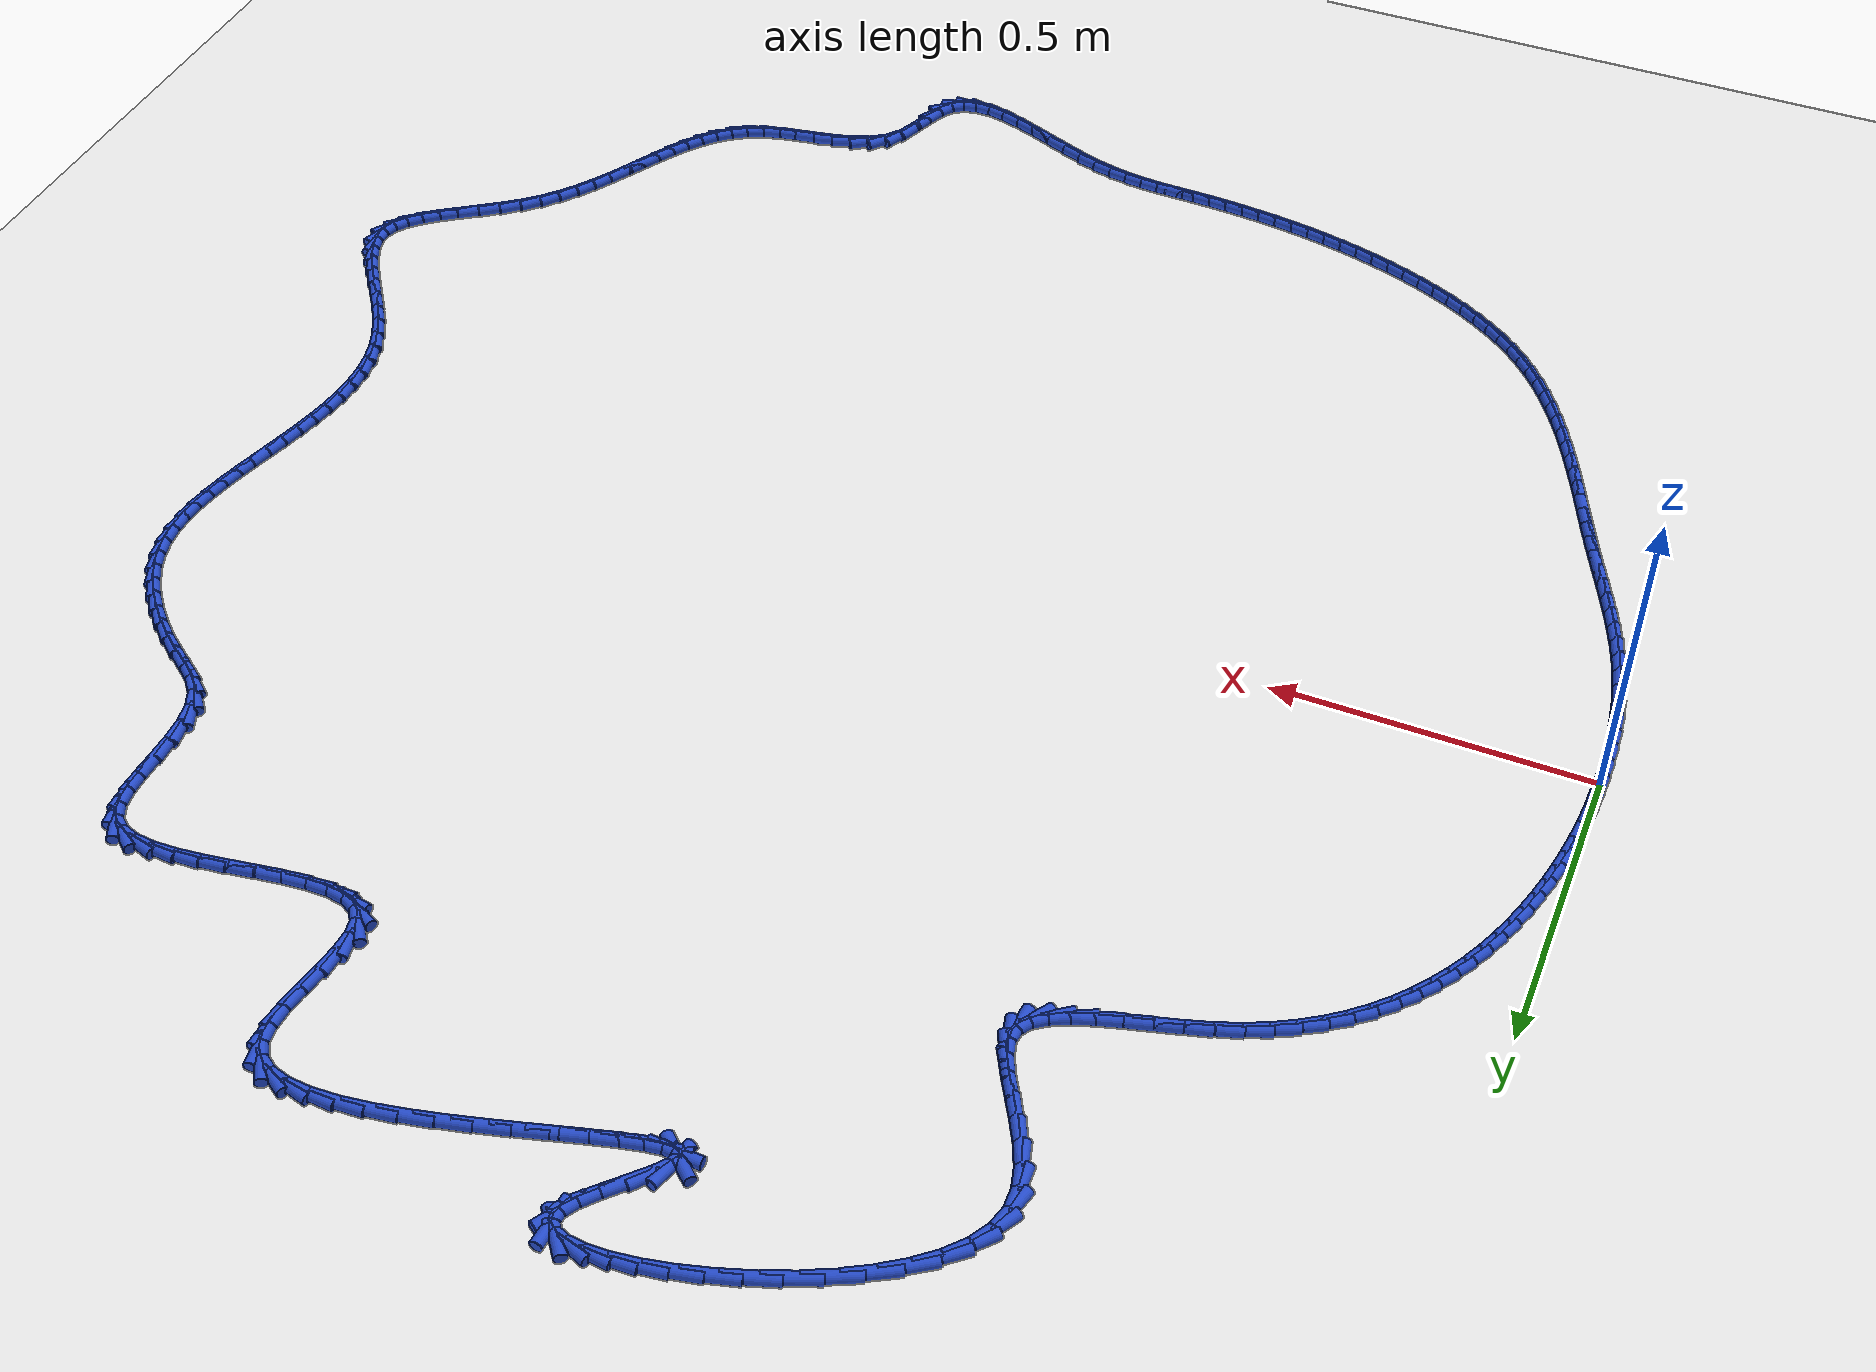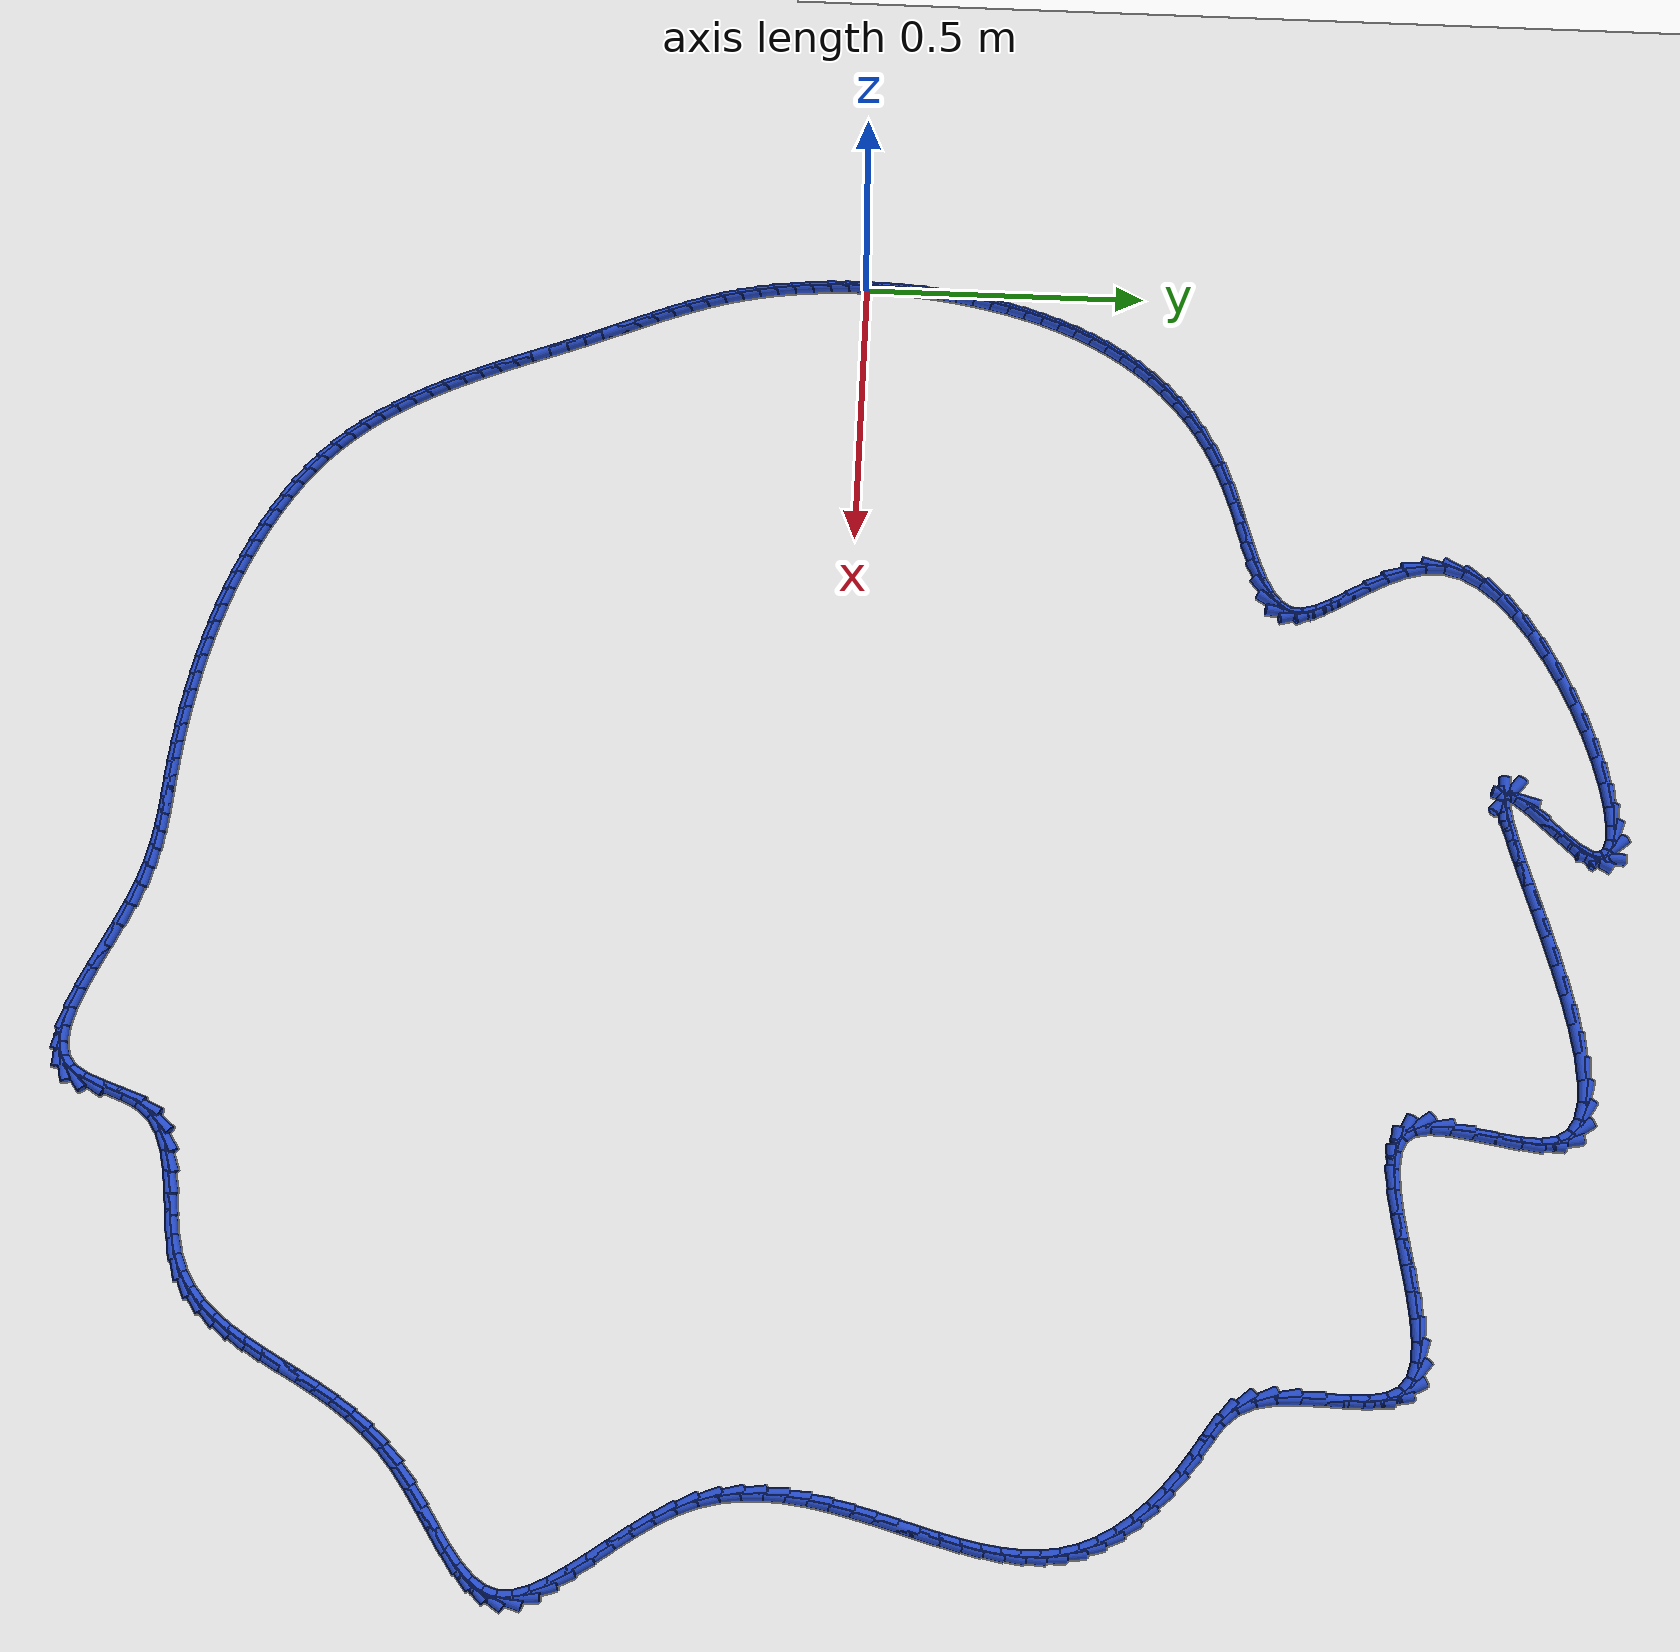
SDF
<sdf version="1.6">
 <world name="default">
  <light name="sun" type="directional">
   <pose>0 0 10 0 -0 0</pose>
   <diffuse>0.8 0.8 0.8 1</diffuse>
   <specular>0.2 0.2 0.2 1</specular>
   <attenuation>
    <range>1000</range>
    <constant>0.9</constant>
    <linear>0.01</linear>
    <quadratic>0.001</quadratic>
   </attenuation>
   <direction>-0.5 0.1 -0.9</direction>
  </light>
  <model name="ground_plane">
   <static>1</static>
   <link name="link">
    <collision name="collision">
     <geometry><plane><normal>0 0 1</normal><size>100 100</size></plane></geometry>
     <surface><friction><ode><mu>100</mu><mu2>50</mu2></ode></friction></surface>
    </collision>
    <visual name="visual">
     <cast_shadows>0</cast_shadows>
     <geometry><plane><normal>0 0 1</normal><size>100 100</size></plane></geometry>
     <material>
      <script><uri>file://media/materials/scripts/gazebo.material</uri><name>Gazebo/WhiteGlow</name></script>
     </material>
    </visual>
   </link>
  </model>
  <gravity>0 0 -9.8</gravity>
  <magnetic_field>6e-06 2.3e-05 -4.2e-05</magnetic_field>
  <atmosphere type="adiabatic"/>
  <physics name="default_physics" default="0" type="ode">
   <max_step_size>0.001</max_step_size>
   <real_time_factor>1</real_time_factor>
   <real_time_update_rate>1000</real_time_update_rate>
  </physics>
  <scene><ambient>0.4 0.4 0.4 1</ambient><background>0.7 0.7 0.7 1</background><shadows>1</shadows></scene>
  <spherical_coordinates>
   <surface_model>EARTH_WGS84</surface_model>
   <latitude_deg>0</latitude_deg>
   <longitude_deg>0</longitude_deg>
   <elevation>0</elevation>
   <heading_deg>0</heading_deg>
  </spherical_coordinates>
  <model name="line">
   <link name="link_0">
    <pose>0.0 -3.469446951953614e-17 0.01 0 1.57 1.551347622708045</pose>
    <collision name="collision">
     <geometry><cylinder><radius>0.01</radius><length>0.08</length></cylinder></geometry>
    </collision>
    <visual name="visual">
     <material>
      <script><name>Gazebo/Blue</name><uri>file://media/materials/scripts/gazebo.material</uri></script>
     </material>
     <geometry><cylinder><radius>0.01</radius><length>0.08</length></cylinder></geometry>
    </visual>
   </link>
   <link name="link_1">
    <pose>0.0006310632778626028 0.032443483434008775 0.01 0 1.57 1.5214623332307498</pose>
    <collision name="collision">
     <geometry><cylinder><radius>0.01</radius><length>0.08</length></cylinder></geometry>
    </collision>
    <visual name="visual">
     <material>
      <script><name>Gazebo/Blue</name><uri>file://media/materials/scripts/gazebo.material</uri></script>
     </material>
     <geometry><cylinder><radius>0.01</radius><length>0.08</length></cylinder></geometry>
    </visual>
   </link>
   <link name="link_2">
    <pose>0.00222877448602239 0.06480280992995505 0.01 0 1.57 1.490794480789097</pose>
    <collision name="collision">
     <geometry><cylinder><radius>0.01</radius><length>0.08</length></cylinder></geometry>
    </collision>
    <visual name="visual">
     <material>
      <script><name>Gazebo/Blue</name><uri>file://media/materials/scripts/gazebo.material</uri></script>
     </material>
     <geometry><cylinder><radius>0.01</radius><length>0.08</length></cylinder></geometry>
    </visual>
   </link>
   <link name="link_3">
    <pose>0.004814420883808927 0.0970536625192309 0.01 0 1.57 1.4593335294211989</pose>
    <collision name="collision">
     <geometry><cylinder><radius>0.01</radius><length>0.08</length></cylinder></geometry>
    </collision>
    <visual name="visual">
     <material>
      <script><name>Gazebo/Blue</name><uri>file://media/materials/scripts/gazebo.material</uri></script>
     </material>
     <geometry><cylinder><radius>0.01</radius><length>0.08</length></cylinder></geometry>
    </visual>
   </link>
   <link name="link_4">
    <pose>0.00840928973055177 0.12917172423322837 0.01 0 1.57 1.4270744777898414</pose>
    <collision name="collision">
     <geometry><cylinder><radius>0.01</radius><length>0.08</length></cylinder></geometry>
    </collision>
    <visual name="visual">
     <material>
      <script><name>Gazebo/Blue</name><uri>file://media/materials/scripts/gazebo.material</uri></script>
     </material>
     <geometry><cylinder><radius>0.01</radius><length>0.08</length></cylinder></geometry>
    </visual>
   </link>
   <link name="link_5">
    <pose>0.013034668285580472 0.16113267810333953 0.01 0 1.57 1.394018565833373</pose>
    <collision name="collision">
     <geometry><cylinder><radius>0.01</radius><length>0.08</length></cylinder></geometry>
    </collision>
    <visual name="visual">
     <material>
      <script><name>Gazebo/Blue</name><uri>file://media/materials/scripts/gazebo.material</uri></script>
     </material>
     <geometry><cylinder><radius>0.01</radius><length>0.08</length></cylinder></geometry>
    </visual>
   </link>
   <link name="link_6">
    <pose>0.018711843808224587 0.19291220716095636 0.01 0 1.57 1.3601739711808627</pose>
    <collision name="collision">
     <geometry><cylinder><radius>0.01</radius><length>0.08</length></cylinder></geometry>
    </collision>
    <visual name="visual">
     <material>
      <script><name>Gazebo/Blue</name><uri>file://media/materials/scripts/gazebo.material</uri></script>
     </material>
     <geometry><cylinder><radius>0.01</radius><length>0.08</length></cylinder></geometry>
    </visual>
   </link>
   <link name="link_7">
    <pose>0.025462103557813684 0.22448599443747105 0.01 0 1.57 1.3255514020256949</pose>
    <collision name="collision">
     <geometry><cylinder><radius>0.01</radius><length>0.08</length></cylinder></geometry>
    </collision>
    <visual name="visual">
     <material>
      <script><name>Gazebo/Blue</name><uri>file://media/materials/scripts/gazebo.material</uri></script>
     </material>
     <geometry><cylinder><radius>0.01</radius><length>0.08</length></cylinder></geometry>
    </visual>
   </link>
   <link name="link_8">
    <pose>0.03330686267905719 0.2558295598063921 0.01 0 1.57 1.2893873009036945</pose>
    <collision name="collision">
     <geometry><cylinder><radius>0.01</radius><length>0.08</length></cylinder></geometry>
    </collision>
    <visual name="visual">
     <material>
      <script><name>Gazebo/Blue</name><uri>file://media/materials/scripts/gazebo.material</uri></script>
     </material>
     <geometry><cylinder><radius>0.01</radius><length>0.08</length></cylinder></geometry>
    </visual>
   </link>
   <link name="link_9">
    <pose>0.04228690338637428 0.28689371437386546 0.01 0 1.57 1.2499902859856358</pose>
    <collision name="collision">
     <geometry><cylinder><radius>0.01</radius><length>0.08</length></cylinder></geometry>
    </collision>
    <visual name="visual">
     <material>
      <script><name>Gazebo/Blue</name><uri>file://media/materials/scripts/gazebo.material</uri></script>
     </material>
     <geometry><cylinder><radius>0.01</radius><length>0.08</length></cylinder></geometry>
    </visual>
   </link>
   <link name="link_10">
    <pose>0.0524829219104767 0.31757834640856647 0.01 0 1.57 1.2070098560567881</pose>
    <collision name="collision">
     <geometry><cylinder><radius>0.01</radius><length>0.08</length></cylinder></geometry>
    </collision>
    <visual name="visual">
     <material>
      <script><name>Gazebo/Blue</name><uri>file://media/materials/scripts/gazebo.material</uri></script>
     </material>
     <geometry><cylinder><radius>0.01</radius><length>0.08</length></cylinder></geometry>
    </visual>
   </link>
   <link name="link_11">
    <pose>0.06398053857860247 0.34777706195076147 0.01 0 1.57 1.1603143816222603</pose>
    <collision name="collision">
     <geometry><cylinder><radius>0.01</radius><length>0.08</length></cylinder></geometry>
    </collision>
    <visual name="visual">
     <material>
      <script><name>Gazebo/Blue</name><uri>file://media/materials/scripts/gazebo.material</uri></script>
     </material>
     <geometry><cylinder><radius>0.01</radius><length>0.08</length></cylinder></geometry>
    </visual>
   </link>
   <link name="link_12">
    <pose>0.07686537371798967 0.37738346704071657 0.01 0 1.57 1.109813871606569</pose>
    <collision name="collision">
     <geometry><cylinder><radius>0.01</radius><length>0.08</length></cylinder></geometry>
    </collision>
    <visual name="visual">
     <material>
      <script><name>Gazebo/Blue</name><uri>file://media/materials/scripts/gazebo.material</uri></script>
     </material>
     <geometry><cylinder><radius>0.01</radius><length>0.08</length></cylinder></geometry>
    </visual>
   </link>
   <link name="link_13">
    <pose>0.09122304765587627 0.4062911677186979 0.01 0 1.57 1.0554810074321803</pose>
    <collision name="collision">
     <geometry><cylinder><radius>0.01</radius><length>0.08</length></cylinder></geometry>
    </collision>
    <visual name="visual">
     <material>
      <script><name>Gazebo/Blue</name><uri>file://media/materials/scripts/gazebo.material</uri></script>
     </material>
     <geometry><cylinder><radius>0.01</radius><length>0.08</length></cylinder></geometry>
    </visual>
   </link>
   <link name="link_14">
    <pose>0.10713918071950027 0.4343937700249714 0.01 0 1.57 0.9973742962797819</pose>
    <collision name="collision">
     <geometry><cylinder><radius>0.01</radius><length>0.08</length></cylinder></geometry>
    </collision>
    <visual name="visual">
     <material>
      <script><name>Gazebo/Blue</name><uri>file://media/materials/scripts/gazebo.material</uri></script>
     </material>
     <geometry><cylinder><radius>0.01</radius><length>0.08</length></cylinder></geometry>
    </visual>
   </link>
   <link name="link_15">
    <pose>0.12469939323609969 0.46158487999980335 0.01 0 1.57 0.9356611636134483</pose>
    <collision name="collision">
     <geometry><cylinder><radius>0.01</radius><length>0.08</length></cylinder></geometry>
    </collision>
    <visual name="visual">
     <material>
      <script><name>Gazebo/Blue</name><uri>file://media/materials/scripts/gazebo.material</uri></script>
     </material>
     <geometry><cylinder><radius>0.01</radius><length>0.08</length></cylinder></geometry>
    </visual>
   </link>
   <link name="link_16">
    <pose>0.1439893055329126 0.48775810368345984 0.01 0 1.57 0.8706375805706945</pose>
    <collision name="collision">
     <geometry><cylinder><radius>0.01</radius><length>0.08</length></cylinder></geometry>
    </collision>
    <visual name="visual">
     <material>
      <script><name>Gazebo/Blue</name><uri>file://media/materials/scripts/gazebo.material</uri></script>
     </material>
     <geometry><cylinder><radius>0.01</radius><length>0.08</length></cylinder></geometry>
    </visual>
   </link>
   <link name="link_17">
    <pose>0.165094537937177 0.5128070471162071 0.01 0 1.57 0.8027398537066995</pose>
    <collision name="collision">
     <geometry><cylinder><radius>0.01</radius><length>0.08</length></cylinder></geometry>
    </collision>
    <visual name="visual">
     <material>
      <script><name>Gazebo/Blue</name><uri>file://media/materials/scripts/gazebo.material</uri></script>
     </material>
     <geometry><cylinder><radius>0.01</radius><length>0.08</length></cylinder></geometry>
    </visual>
   </link>
   <link name="link_18">
    <pose>0.18810071077613086 0.536625316338311 0.01 0 1.57 0.7325440356069635</pose>
    <collision name="collision">
     <geometry><cylinder><radius>0.01</radius><length>0.08</length></cylinder></geometry>
    </collision>
    <visual name="visual">
     <material>
      <script><name>Gazebo/Blue</name><uri>file://media/materials/scripts/gazebo.material</uri></script>
     </material>
     <geometry><cylinder><radius>0.01</radius><length>0.08</length></cylinder></geometry>
    </visual>
   </link>
   <link name="link_19">
    <pose>0.21309344437701214 0.5591065173900378 0.01 0 1.57 0.6607495702812148</pose>
    <collision name="collision">
     <geometry><cylinder><radius>0.01</radius><length>0.08</length></cylinder></geometry>
    </collision>
    <visual name="visual">
     <material>
      <script><name>Gazebo/Blue</name><uri>file://media/materials/scripts/gazebo.material</uri></script>
     </material>
     <geometry><cylinder><radius>0.01</radius><length>0.08</length></cylinder></geometry>
    </visual>
   </link>
   <link name="link_20">
    <pose>0.240158359067059 0.5801442563116536 0.01 0 1.57 0.588146442139677</pose>
    <collision name="collision">
     <geometry><cylinder><radius>0.01</radius><length>0.08</length></cylinder></geometry>
    </collision>
    <visual name="visual">
     <material>
      <script><name>Gazebo/Blue</name><uri>file://media/materials/scripts/gazebo.material</uri></script>
     </material>
     <geometry><cylinder><radius>0.01</radius><length>0.08</length></cylinder></geometry>
    </visual>
   </link>
   <link name="link_21">
    <pose>0.2693810751735095 0.5996321391434246 0.01 0 1.57 0.5155687649617055</pose>
    <collision name="collision">
     <geometry><cylinder><radius>0.01</radius><length>0.08</length></cylinder></geometry>
    </collision>
    <visual name="visual">
     <material>
      <script><name>Gazebo/Blue</name><uri>file://media/materials/scripts/gazebo.material</uri></script>
     </material>
     <geometry><cylinder><radius>0.01</radius><length>0.08</length></cylinder></geometry>
    </visual>
   </link>
   <link name="link_22">
    <pose>0.3008472130236013 0.6174637719256166 0.01 0 1.57 0.44384126703161364</pose>
    <collision name="collision">
     <geometry><cylinder><radius>0.01</radius><length>0.08</length></cylinder></geometry>
    </collision>
    <visual name="visual">
     <material>
      <script><name>Gazebo/Blue</name><uri>file://media/materials/scripts/gazebo.material</uri></script>
     </material>
     <geometry><cylinder><radius>0.01</radius><length>0.08</length></cylinder></geometry>
    </visual>
   </link>
   <link name="link_23">
    <pose>0.3346423929445729 0.6335327606984963 0.01 0 1.57 0.3737866147968108</pose>
    <collision name="collision">
     <geometry><cylinder><radius>0.01</radius><length>0.08</length></cylinder></geometry>
    </collision>
    <visual name="visual">
     <material>
      <script><name>Gazebo/Blue</name><uri>file://media/materials/scripts/gazebo.material</uri></script>
     </material>
     <geometry><cylinder><radius>0.01</radius><length>0.08</length></cylinder></geometry>
    </visual>
   </link>
   <link name="link_24">
    <pose>0.3708493988317719 0.6477340845346052 0.01 0 1.57 0.3148942566973578</pose>
    <collision name="collision">
     <geometry><cylinder><radius>0.01</radius><length>0.08</length></cylinder></geometry>
    </collision>
    <visual name="visual">
     <material>
      <script><name>Gazebo/Blue</name><uri>file://media/materials/scripts/gazebo.material</uri></script>
     </material>
     <geometry><cylinder><radius>0.01</radius><length>0.08</length></cylinder></geometry>
    </visual>
   </link>
   <link name="link_25">
    <pose>0.4090845612367298 0.6601885186902318 0.01 0 1.57 0.28279651600928557</pose>
    <collision name="collision">
     <geometry><cylinder><radius>0.01</radius><length>0.08</length></cylinder></geometry>
    </collision>
    <visual name="visual">
     <material>
      <script><name>Gazebo/Blue</name><uri>file://media/materials/scripts/gazebo.material</uri></script>
     </material>
     <geometry><cylinder><radius>0.01</radius><length>0.08</length></cylinder></geometry>
    </visual>
   </link>
   <link name="link_26">
    <pose>0.44798301336738394 0.6714918068587505 0.01 0 1.57 0.27659774655328795</pose>
    <collision name="collision">
     <geometry><cylinder><radius>0.01</radius><length>0.08</length></cylinder></geometry>
    </collision>
    <visual name="visual">
     <material>
      <script><name>Gazebo/Blue</name><uri>file://media/materials/scripts/gazebo.material</uri></script>
     </material>
     <geometry><cylinder><radius>0.01</radius><length>0.08</length></cylinder></geometry>
    </visual>
   </link>
   <link name="link_27">
    <pose>0.48605588649348863 0.6822997183819521 0.01 0 1.57 0.2976227414882241</pose>
    <collision name="collision">
     <geometry><cylinder><radius>0.01</radius><length>0.08</length></cylinder></geometry>
    </collision>
    <visual name="visual">
     <material>
      <script><name>Gazebo/Blue</name><uri>file://media/materials/scripts/gazebo.material</uri></script>
     </material>
     <geometry><cylinder><radius>0.01</radius><length>0.08</length></cylinder></geometry>
    </visual>
   </link>
   <link name="link_28">
    <pose>0.5218143118847985 0.6932680226016271 0.01 0 1.57 0.3533080853779067</pose>
    <collision name="collision">
     <geometry><cylinder><radius>0.01</radius><length>0.08</length></cylinder></geometry>
    </collision>
    <visual name="visual">
     <material>
      <script><name>Gazebo/Blue</name><uri>file://media/materials/scripts/gazebo.material</uri></script>
     </material>
     <geometry><cylinder><radius>0.01</radius><length>0.08</length></cylinder></geometry>
    </visual>
   </link>
   <link name="link_29">
    <pose>0.5537694208110685 0.705052488859567 0.01 0 1.57 0.46139283071344844</pose>
    <collision name="collision">
     <geometry><cylinder><radius>0.01</radius><length>0.08</length></cylinder></geometry>
    </collision>
    <visual name="visual">
     <material>
      <script><name>Gazebo/Blue</name><uri>file://media/materials/scripts/gazebo.material</uri></script>
     </material>
     <geometry><cylinder><radius>0.01</radius><length>0.08</length></cylinder></geometry>
    </visual>
   </link>
   <link name="link_30">
    <pose>0.580432344542053 0.7183088864975622 0.01 0 1.57 0.658544431414146</pose>
    <collision name="collision">
     <geometry><cylinder><radius>0.01</radius><length>0.08</length></cylinder></geometry>
    </collision>
    <visual name="visual">
     <material>
      <script><name>Gazebo/Blue</name><uri>file://media/materials/scripts/gazebo.material</uri></script>
     </material>
     <geometry><cylinder><radius>0.01</radius><length>0.08</length></cylinder></geometry>
    </visual>
   </link>
   <link name="link_31">
    <pose>0.6003142143475064 0.7336929848574038 0.01 0 1.57 1.0020806790082801</pose>
    <collision name="collision">
     <geometry><cylinder><radius>0.01</radius><length>0.08</length></cylinder></geometry>
    </collision>
    <visual name="visual">
     <material>
      <script><name>Gazebo/Blue</name><uri>file://media/materials/scripts/gazebo.material</uri></script>
     </material>
     <geometry><cylinder><radius>0.01</radius><length>0.08</length></cylinder></geometry>
    </visual>
   </link>
   <link name="link_32">
    <pose>0.6119261614971837 0.7518605532808826 0.01 0 1.57 1.4758298179137297</pose>
    <collision name="collision">
     <geometry><cylinder><radius>0.01</radius><length>0.08</length></cylinder></geometry>
    </collision>
    <visual name="visual">
     <material>
      <script><name>Gazebo/Blue</name><uri>file://media/materials/scripts/gazebo.material</uri></script>
     </material>
     <geometry><cylinder><radius>0.01</radius><length>0.08</length></cylinder></geometry>
    </visual>
   </link>
   <link name="link_33">
    <pose>0.6139784881230772 0.7734066036426206 0.01 0 1.57 -1.312101001811424</pose>
    <collision name="collision">
     <geometry><cylinder><radius>0.01</radius><length>0.08</length></cylinder></geometry>
    </collision>
    <visual name="visual">
     <material>
      <script><name>Gazebo/Blue</name><uri>file://media/materials/scripts/gazebo.material</uri></script>
     </material>
     <geometry><cylinder><radius>0.01</radius><length>0.08</length></cylinder></geometry>
    </visual>
   </link>
   <link name="link_34">
    <pose>0.6074048576649154 0.7982479070337151 0.01 0 1.57 -1.134745780756237</pose>
    <collision name="collision">
     <geometry><cylinder><radius>0.01</radius><length>0.08</length></cylinder></geometry>
    </collision>
    <visual name="visual">
     <material>
      <script><name>Gazebo/Blue</name><uri>file://media/materials/scripts/gazebo.material</uri></script>
     </material>
     <geometry><cylinder><radius>0.01</radius><length>0.08</length></cylinder></geometry>
    </visual>
   </link>
   <link name="link_35">
    <pose>0.5945308500287122 0.8258766276622478 0.01 0 1.57 -1.058211550674028</pose>
    <collision name="collision">
     <geometry><cylinder><radius>0.01</radius><length>0.08</length></cylinder></geometry>
    </collision>
    <visual name="visual">
     <material>
      <script><name>Gazebo/Blue</name><uri>file://media/materials/scripts/gazebo.material</uri></script>
     </material>
     <geometry><cylinder><radius>0.01</radius><length>0.08</length></cylinder></geometry>
    </visual>
   </link>
   <link name="link_36">
    <pose>0.5777034065088035 0.8557784134023594 0.01 0 1.57 -1.043539684821418</pose>
    <collision name="collision">
     <geometry><cylinder><radius>0.01</radius><length>0.08</length></cylinder></geometry>
    </collision>
    <visual name="visual">
     <material>
      <script><name>Gazebo/Blue</name><uri>file://media/materials/scripts/gazebo.material</uri></script>
     </material>
     <geometry><cylinder><radius>0.01</radius><length>0.08</length></cylinder></geometry>
    </visual>
   </link>
   <link name="link_37">
    <pose>0.5592694683995242 0.8874389121281911 0.01 0 1.57 -1.0774325841149117</pose>
    <collision name="collision">
     <geometry><cylinder><radius>0.01</radius><length>0.08</length></cylinder></geometry>
    </collision>
    <visual name="visual">
     <material>
      <script><name>Gazebo/Blue</name><uri>file://media/materials/scripts/gazebo.material</uri></script>
     </material>
     <geometry><cylinder><radius>0.01</radius><length>0.08</length></cylinder></geometry>
    </visual>
   </link>
   <link name="link_38">
    <pose>0.5415759769952098 0.9203437717138842 0.01 0 1.57 -1.161112958504543</pose>
    <collision name="collision">
     <geometry><cylinder><radius>0.01</radius><length>0.08</length></cylinder></geometry>
    </collision>
    <visual name="visual">
     <material>
      <script><name>Gazebo/Blue</name><uri>file://media/materials/scripts/gazebo.material</uri></script>
     </material>
     <geometry><cylinder><radius>0.01</radius><length>0.08</length></cylinder></geometry>
    </visual>
   </link>
   <link name="link_39">
    <pose>0.5269698735901955 0.9539786400335792 0.01 0 1.57 -1.3061999585849446</pose>
    <collision name="collision">
     <geometry><cylinder><radius>0.01</radius><length>0.08</length></cylinder></geometry>
    </collision>
    <visual name="visual">
     <material>
      <script><name>Gazebo/Blue</name><uri>file://media/materials/scripts/gazebo.material</uri></script>
     </material>
     <geometry><cylinder><radius>0.01</radius><length>0.08</length></cylinder></geometry>
    </visual>
   </link>
   <link name="link_40">
    <pose>0.5177980994788169 0.9878291649614179 0.01 0 1.57 -1.5293765807955133</pose>
    <collision name="collision">
     <geometry><cylinder><radius>0.01</radius><length>0.08</length></cylinder></geometry>
    </collision>
    <visual name="visual">
     <material>
      <script><name>Gazebo/Blue</name><uri>file://media/materials/scripts/gazebo.material</uri></script>
     </material>
     <geometry><cylinder><radius>0.01</radius><length>0.08</length></cylinder></geometry>
    </visual>
   </link>
   <link name="link_41">
    <pose>0.5164075959554093 1.0213809943715408 0.01 0 1.57 1.319639766445815</pose>
    <collision name="collision">
     <geometry><cylinder><radius>0.01</radius><length>0.08</length></cylinder></geometry>
    </collision>
    <visual name="visual">
     <material>
      <script><name>Gazebo/Blue</name><uri>file://media/materials/scripts/gazebo.material</uri></script>
     </material>
     <geometry><cylinder><radius>0.01</radius><length>0.08</length></cylinder></geometry>
    </visual>
   </link>
   <link name="link_42">
    <pose>0.5248132688190369 1.0541421649048626 0.01 0 1.57 1.0565491156961648</pose>
    <collision name="collision">
     <geometry><cylinder><radius>0.01</radius><length>0.08</length></cylinder></geometry>
    </collision>
    <visual name="visual">
     <material>
      <script><name>Gazebo/Blue</name><uri>file://media/materials/scripts/gazebo.material</uri></script>
     </material>
     <geometry><cylinder><radius>0.01</radius><length>0.08</length></cylinder></geometry>
    </visual>
   </link>
   <link name="link_43">
    <pose>0.5426862968222728 1.0857787479876455 0.01 0 1.57 0.8606946901196671</pose>
    <collision name="collision">
     <geometry><cylinder><radius>0.01</radius><length>0.08</length></cylinder></geometry>
    </collision>
    <visual name="visual">
     <material>
      <script><name>Gazebo/Blue</name><uri>file://media/materials/scripts/gazebo.material</uri></script>
     </material>
     <geometry><cylinder><radius>0.01</radius><length>0.08</length></cylinder></geometry>
    </visual>
   </link>
   <link name="link_44">
    <pose>0.5686890252021204 1.1160248395152679 0.01 0 1.57 0.7170650592184831</pose>
    <collision name="collision">
     <geometry><cylinder><radius>0.01</radius><length>0.08</length></cylinder></geometry>
    </collision>
    <visual name="visual">
     <material>
      <script><name>Gazebo/Blue</name><uri>file://media/materials/scripts/gazebo.material</uri></script>
     </material>
     <geometry><cylinder><radius>0.01</radius><length>0.08</length></cylinder></geometry>
    </visual>
   </link>
   <link name="link_45">
    <pose>0.6014798675906796 1.1446148004866477 0.01 0 1.57 0.609004369966287</pose>
    <collision name="collision">
     <geometry><cylinder><radius>0.01</radius><length>0.08</length></cylinder></geometry>
    </collision>
    <visual name="visual">
     <material>
      <script><name>Gazebo/Blue</name><uri>file://media/materials/scripts/gazebo.material</uri></script>
     </material>
     <geometry><cylinder><radius>0.01</radius><length>0.08</length></cylinder></geometry>
    </visual>
   </link>
   <link name="link_46">
    <pose>0.6397172376200493 1.1712829919007028 0.01 0 1.57 0.5242085539335282</pose>
    <collision name="collision">
     <geometry><cylinder><radius>0.01</radius><length>0.08</length></cylinder></geometry>
    </collision>
    <visual name="visual">
     <material>
      <script><name>Gazebo/Blue</name><uri>file://media/materials/scripts/gazebo.material</uri></script>
     </material>
     <geometry><cylinder><radius>0.01</radius><length>0.08</length></cylinder></geometry>
    </visual>
   </link>
   <link name="link_47">
    <pose>0.6820595489223289 1.1957637747563508 0.01 0 1.57 0.4542911078282176</pose>
    <collision name="collision">
     <geometry><cylinder><radius>0.01</radius><length>0.08</length></cylinder></geometry>
    </collision>
    <visual name="visual">
     <material>
      <script><name>Gazebo/Blue</name><uri>file://media/materials/scripts/gazebo.material</uri></script>
     </material>
     <geometry><cylinder><radius>0.01</radius><length>0.08</length></cylinder></geometry>
    </visual>
   </link>
   <link name="link_48">
    <pose>0.7271652151296177 1.2177915100525087 0.01 0 1.57 0.39337315590906513</pose>
    <collision name="collision">
     <geometry><cylinder><radius>0.01</radius><length>0.08</length></cylinder></geometry>
    </collision>
    <visual name="visual">
     <material>
      <script><name>Gazebo/Blue</name><uri>file://media/materials/scripts/gazebo.material</uri></script>
     </material>
     <geometry><cylinder><radius>0.01</radius><length>0.08</length></cylinder></geometry>
    </visual>
   </link>
   <link name="link_49">
    <pose>0.7736926498740148 1.2371005587880954 0.01 0 1.57 0.3369052658944641</pose>
    <collision name="collision">
     <geometry><cylinder><radius>0.01</radius><length>0.08</length></cylinder></geometry>
    </collision>
    <visual name="visual">
     <material>
      <script><name>Gazebo/Blue</name><uri>file://media/materials/scripts/gazebo.material</uri></script>
     </material>
     <geometry><cylinder><radius>0.01</radius><length>0.08</length></cylinder></geometry>
    </visual>
   </link>
   <link name="link_50">
    <pose>0.8203002667876199 1.2534252819620282 0.01 0 1.57 0.28071801904414695</pose>
    <collision name="collision">
     <geometry><cylinder><radius>0.01</radius><length>0.08</length></cylinder></geometry>
    </collision>
    <visual name="visual">
     <material>
      <script><name>Gazebo/Blue</name><uri>file://media/materials/scripts/gazebo.material</uri></script>
     </material>
     <geometry><cylinder><radius>0.01</radius><length>0.08</length></cylinder></geometry>
    </visual>
   </link>
   <link name="link_51">
    <pose>0.8656464795025323 1.2665000405732247 0.01 0 1.57 0.2200209540827201</pose>
    <collision name="collision">
     <geometry><cylinder><radius>0.01</radius><length>0.08</length></cylinder></geometry>
    </collision>
    <visual name="visual">
     <material>
      <script><name>Gazebo/Blue</name><uri>file://media/materials/scripts/gazebo.material</uri></script>
     </material>
     <geometry><cylinder><radius>0.01</radius><length>0.08</length></cylinder></geometry>
    </visual>
   </link>
   <link name="link_52">
    <pose>0.9083897016508508 1.2760591956206029 0.01 0 1.57 0.14783400576240263</pose>
    <collision name="collision">
     <geometry><cylinder><radius>0.01</radius><length>0.08</length></cylinder></geometry>
    </collision>
    <visual name="visual">
     <material>
      <script><name>Gazebo/Blue</name><uri>file://media/materials/scripts/gazebo.material</uri></script>
     </material>
     <geometry><cylinder><radius>0.01</radius><length>0.08</length></cylinder></geometry>
    </visual>
   </link>
   <link name="link_53">
    <pose>0.9471883468646749 1.2818371081030806 0.01 0 1.57 0.051607454191733446</pose>
    <collision name="collision">
     <geometry><cylinder><radius>0.01</radius><length>0.08</length></cylinder></geometry>
    </collision>
    <visual name="visual">
     <material>
      <script><name>Gazebo/Blue</name><uri>file://media/materials/scripts/gazebo.material</uri></script>
     </material>
     <geometry><cylinder><radius>0.01</radius><length>0.08</length></cylinder></geometry>
    </visual>
   </link>
   <link name="link_54">
    <pose>0.9807008287761048 1.283568139019576 0.01 0 1.57 -0.0957271763182718</pose>
    <collision name="collision">
     <geometry><cylinder><radius>0.01</radius><length>0.08</length></cylinder></geometry>
    </collision>
    <visual name="visual">
     <material>
      <script><name>Gazebo/Blue</name><uri>file://media/materials/scripts/gazebo.material</uri></script>
     </material>
     <geometry><cylinder><radius>0.01</radius><length>0.08</length></cylinder></geometry>
    </visual>
   </link>
   <link name="link_55">
    <pose>1.0075855610172384 1.2809866493690059 0.01 0 1.57 -0.3618435693640887</pose>
    <collision name="collision">
     <geometry><cylinder><radius>0.01</radius><length>0.08</length></cylinder></geometry>
    </collision>
    <visual name="visual">
     <material>
      <script><name>Gazebo/Blue</name><uri>file://media/materials/scripts/gazebo.material</uri></script>
     </material>
     <geometry><cylinder><radius>0.01</radius><length>0.08</length></cylinder></geometry>
    </visual>
   </link>
   <link name="link_56">
    <pose>1.0265009572201764 1.2738270001502887 0.01 0 1.57 -0.895968242592329</pose>
    <collision name="collision">
     <geometry><cylinder><radius>0.01</radius><length>0.08</length></cylinder></geometry>
    </collision>
    <visual name="visual">
     <material>
      <script><name>Gazebo/Blue</name><uri>file://media/materials/scripts/gazebo.material</uri></script>
     </material>
     <geometry><cylinder><radius>0.01</radius><length>0.08</length></cylinder></geometry>
    </visual>
   </link>
   <link name="link_57">
    <pose>1.0361054310170168 1.2618235523623418 0.01 0 1.57 1.5096302738706202</pose>
    <collision name="collision">
     <geometry><cylinder><radius>0.01</radius><length>0.08</length></cylinder></geometry>
    </collision>
    <visual name="visual">
     <material>
      <script><name>Gazebo/Blue</name><uri>file://media/materials/scripts/gazebo.material</uri></script>
     </material>
     <geometry><cylinder><radius>0.01</radius><length>0.08</length></cylinder></geometry>
    </visual>
   </link>
   <link name="link_58">
    <pose>1.03505739603986 1.2447106670040835 0.01 0 1.57 1.0516517662364486</pose>
    <collision name="collision">
     <geometry><cylinder><radius>0.01</radius><length>0.08</length></cylinder></geometry>
    </collision>
    <visual name="visual">
     <material>
      <script><name>Gazebo/Blue</name><uri>file://media/materials/scripts/gazebo.material</uri></script>
     </material>
     <geometry><cylinder><radius>0.01</radius><length>0.08</length></cylinder></geometry>
    </visual>
   </link>
   <link name="link_59">
    <pose>1.0222752182474473 1.2223417751878534 0.01 0 1.57 0.8737442590883272</pose>
    <collision name="collision">
     <geometry><cylinder><radius>0.01</radius><length>0.08</length></cylinder></geometry>
    </collision>
    <visual name="visual">
     <material>
      <script><name>Gazebo/Blue</name><uri>file://media/materials/scripts/gazebo.material</uri></script>
     </material>
     <geometry><cylinder><radius>0.01</radius><length>0.08</length></cylinder></geometry>
    </visual>
   </link>
   <link name="link_60">
    <pose>1.0004826008522436 1.1963133273875095 0.01 0 1.57 0.815732766385355</pose>
    <collision name="collision">
     <geometry><cylinder><radius>0.01</radius><length>0.08</length></cylinder></geometry>
    </collision>
    <visual name="visual">
     <material>
      <script><name>Gazebo/Blue</name><uri>file://media/materials/scripts/gazebo.material</uri></script>
     </material>
     <geometry><cylinder><radius>0.01</radius><length>0.08</length></cylinder></geometry>
    </visual>
   </link>
   <link name="link_61">
    <pose>0.9752900682114598 1.1695440708440654 0.01 0 1.57 0.8201089405374283</pose>
    <collision name="collision">
     <geometry><cylinder><radius>0.01</radius><length>0.08</length></cylinder></geometry>
    </collision>
    <visual name="visual">
     <material>
      <script><name>Gazebo/Blue</name><uri>file://media/materials/scripts/gazebo.material</uri></script>
     </material>
     <geometry><cylinder><radius>0.01</radius><length>0.08</length></cylinder></geometry>
    </visual>
   </link>
   <link name="link_62">
    <pose>0.9523799879213143 1.144985660304029 0.01 0 1.57 0.9139286673673777</pose>
    <collision name="collision">
     <geometry><cylinder><radius>0.01</radius><length>0.08</length></cylinder></geometry>
    </collision>
    <visual name="visual">
     <material>
      <script><name>Gazebo/Blue</name><uri>file://media/materials/scripts/gazebo.material</uri></script>
     </material>
     <geometry><cylinder><radius>0.01</radius><length>0.08</length></cylinder></geometry>
    </visual>
   </link>
   <link name="link_63">
    <pose>0.937415770065643 1.1255792840652181 0.01 0 1.57 1.2947535767993004</pose>
    <collision name="collision">
     <geometry><cylinder><radius>0.01</radius><length>0.08</length></cylinder></geometry>
    </collision>
    <visual name="visual">
     <material>
      <script><name>Gazebo/Blue</name><uri>file://media/materials/scripts/gazebo.material</uri></script>
     </material>
     <geometry><cylinder><radius>0.01</radius><length>0.08</length></cylinder></geometry>
    </visual>
   </link>
   <link name="link_64">
    <pose>0.933868107428264 1.1130555304981562 0.01 0 1.57 -0.7180120632977532</pose>
    <collision name="collision">
     <geometry><cylinder><radius>0.01</radius><length>0.08</length></cylinder></geometry>
    </collision>
    <visual name="visual">
     <material>
      <script><name>Gazebo/Blue</name><uri>file://media/materials/scripts/gazebo.material</uri></script>
     </material>
     <geometry><cylinder><radius>0.01</radius><length>0.08</length></cylinder></geometry>
    </visual>
   </link>
   <link name="link_65">
    <pose>0.94100245315866 1.1068232738173547 0.01 0 1.57 -0.04781191547302565</pose>
    <collision name="collision">
     <geometry><cylinder><radius>0.01</radius><length>0.08</length></cylinder></geometry>
    </collision>
    <visual name="visual">
     <material>
      <script><name>Gazebo/Blue</name><uri>file://media/materials/scripts/gazebo.material</uri></script>
     </material>
     <geometry><cylinder><radius>0.01</radius><length>0.08</length></cylinder></geometry>
    </visual>
   </link>
   <link name="link_66">
    <pose>0.9576084676548963 1.1060287029060842 0.01 0 1.57 0.1512174634362945</pose>
    <collision name="collision">
     <geometry><cylinder><radius>0.01</radius><length>0.08</length></cylinder></geometry>
    </collision>
    <visual name="visual">
     <material>
      <script><name>Gazebo/Blue</name><uri>file://media/materials/scripts/gazebo.material</uri></script>
     </material>
     <geometry><cylinder><radius>0.01</radius><length>0.08</length></cylinder></geometry>
    </visual>
   </link>
   <link name="link_67">
    <pose>0.9824758113150382 1.1098180066476155 0.01 0 1.57 0.23136291057843697</pose>
    <collision name="collision">
     <geometry><cylinder><radius>0.01</radius><length>0.08</length></cylinder></geometry>
    </collision>
    <visual name="visual">
     <material>
      <script><name>Gazebo/Blue</name><uri>file://media/materials/scripts/gazebo.material</uri></script>
     </material>
     <geometry><cylinder><radius>0.01</radius><length>0.08</length></cylinder></geometry>
    </visual>
   </link>
   <link name="link_68">
    <pose>1.014394144537151 1.1173373739252188 0.01 0 1.57 0.26865916935724266</pose>
    <collision name="collision">
     <geometry><cylinder><radius>0.01</radius><length>0.08</length></cylinder></geometry>
    </collision>
    <visual name="visual">
     <material>
      <script><name>Gazebo/Blue</name><uri>file://media/materials/scripts/gazebo.material</uri></script>
     </material>
     <geometry><cylinder><radius>0.01</radius><length>0.08</length></cylinder></geometry>
    </visual>
   </link>
   <link name="link_69">
    <pose>1.0521531277193006 1.1277329936221654 0.01 0 1.57 0.2849789727118552</pose>
    <collision name="collision">
     <geometry><cylinder><radius>0.01</radius><length>0.08</length></cylinder></geometry>
    </collision>
    <visual name="visual">
     <material>
      <script><name>Gazebo/Blue</name><uri>file://media/materials/scripts/gazebo.material</uri></script>
     </material>
     <geometry><cylinder><radius>0.01</radius><length>0.08</length></cylinder></geometry>
    </visual>
   </link>
   <link name="link_70">
    <pose>1.0945424212595523 1.1401510546217255 0.01 0 1.57 0.28832786305315156</pose>
    <collision name="collision">
     <geometry><cylinder><radius>0.01</radius><length>0.08</length></cylinder></geometry>
    </collision>
    <visual name="visual">
     <material>
      <script><name>Gazebo/Blue</name><uri>file://media/materials/scripts/gazebo.material</uri></script>
     </material>
     <geometry><cylinder><radius>0.01</radius><length>0.08</length></cylinder></geometry>
    </visual>
   </link>
   <link name="link_71">
    <pose>1.1403516855559714 1.1537377458071698 0.01 0 1.57 0.28179691725811556</pose>
    <collision name="collision">
     <geometry><cylinder><radius>0.01</radius><length>0.08</length></cylinder></geometry>
    </collision>
    <visual name="visual">
     <material>
      <script><name>Gazebo/Blue</name><uri>file://media/materials/scripts/gazebo.material</uri></script>
     </material>
     <geometry><cylinder><radius>0.01</radius><length>0.08</length></cylinder></geometry>
    </visual>
   </link>
   <link name="link_72">
    <pose>1.1883705810066232 1.1676392560617692 0.01 0 1.57 0.2661366302641057</pose>
    <collision name="collision">
     <geometry><cylinder><radius>0.01</radius><length>0.08</length></cylinder></geometry>
    </collision>
    <visual name="visual">
     <material>
      <script><name>Gazebo/Blue</name><uri>file://media/materials/scripts/gazebo.material</uri></script>
     </material>
     <geometry><cylinder><radius>0.01</radius><length>0.08</length></cylinder></geometry>
    </visual>
   </link>
   <link name="link_73">
    <pose>1.237388768009573 1.1810017742687935 0.01 0 1.57 0.24049854575931093</pose>
    <collision name="collision">
     <geometry><cylinder><radius>0.01</radius><length>0.08</length></cylinder></geometry>
    </collision>
    <visual name="visual">
     <material>
      <script><name>Gazebo/Blue</name><uri>file://media/materials/scripts/gazebo.material</uri></script>
     </material>
     <geometry><cylinder><radius>0.01</radius><length>0.08</length></cylinder></geometry>
    </visual>
   </link>
   <link name="link_74">
    <pose>1.2861959069628872 1.1929714893115142 0.01 0 1.57 0.2023813010103762</pose>
    <collision name="collision">
     <geometry><cylinder><radius>0.01</radius><length>0.08</length></cylinder></geometry>
    </collision>
    <visual name="visual">
     <material>
      <script><name>Gazebo/Blue</name><uri>file://media/materials/scripts/gazebo.material</uri></script>
     </material>
     <geometry><cylinder><radius>0.01</radius><length>0.08</length></cylinder></geometry>
    </visual>
   </link>
   <link name="link_75">
    <pose>1.33358165826463 1.2026945900732016 0.01 0 1.57 0.1469132653189109</pose>
    <collision name="collision">
     <geometry><cylinder><radius>0.01</radius><length>0.08</length></cylinder></geometry>
    </collision>
    <visual name="visual">
     <material>
      <script><name>Gazebo/Blue</name><uri>file://media/materials/scripts/gazebo.material</uri></script>
     </material>
     <geometry><cylinder><radius>0.01</radius><length>0.08</length></cylinder></geometry>
    </visual>
   </link>
   <link name="link_76">
    <pose>1.3783356823128683 1.2093172654371265 0.01 0 1.57 0.06513167962352281</pose>
    <collision name="collision">
     <geometry><cylinder><radius>0.01</radius><length>0.08</length></cylinder></geometry>
    </collision>
    <visual name="visual">
     <material>
      <script><name>Gazebo/Blue</name><uri>file://media/materials/scripts/gazebo.material</uri></script>
     </material>
     <geometry><cylinder><radius>0.01</radius><length>0.08</length></cylinder></geometry>
    </visual>
   </link>
   <link name="link_77">
    <pose>1.4192476395056661 1.211985704286559 0.01 0 1.57 -0.05959570302389738</pose>
    <collision name="collision">
     <geometry><cylinder><radius>0.01</radius><length>0.08</length></cylinder></geometry>
    </collision>
    <visual name="visual">
     <material>
      <script><name>Gazebo/Blue</name><uri>file://media/materials/scripts/gazebo.material</uri></script>
     </material>
     <geometry><cylinder><radius>0.01</radius><length>0.08</length></cylinder></geometry>
    </visual>
   </link>
   <link name="link_78">
    <pose>1.45510719024109 1.2098460955047705 0.01 0 1.57 -0.25772923761039124</pose>
    <collision name="collision">
     <geometry><cylinder><radius>0.01</radius><length>0.08</length></cylinder></geometry>
    </collision>
    <visual name="visual">
     <material>
      <script><name>Gazebo/Blue</name><uri>file://media/materials/scripts/gazebo.material</uri></script>
     </material>
     <geometry><cylinder><radius>0.01</radius><length>0.08</length></cylinder></geometry>
    </visual>
   </link>
   <link name="link_79">
    <pose>1.4847039949172043 1.202044627975031 0.01 0 1.57 -0.5743618523126905</pose>
    <collision name="collision">
     <geometry><cylinder><radius>0.01</radius><length>0.08</length></cylinder></geometry>
    </collision>
    <visual name="visual">
     <material>
      <script><name>Gazebo/Blue</name><uri>file://media/materials/scripts/gazebo.material</uri></script>
     </material>
     <geometry><cylinder><radius>0.01</radius><length>0.08</length></cylinder></geometry>
    </visual>
   </link>
   <link name="link_80">
    <pose>1.5068277139320752 1.1877274905806114 0.01 0 1.57 -1.0149696693725823</pose>
    <collision name="collision">
     <geometry><cylinder><radius>0.01</radius><length>0.08</length></cylinder></geometry>
    </collision>
    <visual name="visual">
     <material>
      <script><name>Gazebo/Blue</name><uri>file://media/materials/scripts/gazebo.material</uri></script>
     </material>
     <geometry><cylinder><radius>0.01</radius><length>0.08</length></cylinder></geometry>
    </visual>
   </link>
   <link name="link_81">
    <pose>1.5202881023047141 1.1660574138541357 0.01 0 1.57 -1.4005337293153604</pose>
    <collision name="collision">
     <geometry><cylinder><radius>0.01</radius><length>0.08</length></cylinder></geometry>
    </collision>
    <visual name="visual">
     <material>
      <script><name>Gazebo/Blue</name><uri>file://media/materials/scripts/gazebo.material</uri></script>
     </material>
     <geometry><cylinder><radius>0.01</radius><length>0.08</length></cylinder></geometry>
    </visual>
   </link>
   <link name="link_82">
    <pose>1.525232579244535 1.1372982773396787 0.01 0 1.57 1.5332250288218687</pose>
    <collision name="collision">
     <geometry><cylinder><radius>0.01</radius><length>0.08</length></cylinder></geometry>
    </collision>
    <visual name="visual">
     <material>
      <script><name>Gazebo/Blue</name><uri>file://media/materials/scripts/gazebo.material</uri></script>
     </material>
     <geometry><cylinder><radius>0.01</radius><length>0.08</length></cylinder></geometry>
    </visual>
   </link>
   <link name="link_83">
    <pose>1.5239616225004422 1.1034863323763935 0.01 0 1.57 1.4355130489868508</pose>
    <collision name="collision">
     <geometry><cylinder><radius>0.01</radius><length>0.08</length></cylinder></geometry>
    </collision>
    <visual name="visual">
     <material>
      <script><name>Gazebo/Blue</name><uri>file://media/materials/scripts/gazebo.material</uri></script>
     </material>
     <geometry><cylinder><radius>0.01</radius><length>0.08</length></cylinder></geometry>
    </visual>
   </link>
   <link name="link_84">
    <pose>1.5189705553915855 1.0668182248244193 0.01 0 1.57 1.4057888394384377</pose>
    <collision name="collision">
     <geometry><cylinder><radius>0.01</radius><length>0.08</length></cylinder></geometry>
    </collision>
    <visual name="visual">
     <material>
      <script><name>Gazebo/Blue</name><uri>file://media/materials/scripts/gazebo.material</uri></script>
     </material>
     <geometry><cylinder><radius>0.01</radius><length>0.08</length></cylinder></geometry>
    </visual>
   </link>
   <link name="link_85">
    <pose>1.5127547012371125 1.029490600543895 0.01 0 1.57 1.4334916759753886</pose>
    <collision name="collision">
     <geometry><cylinder><radius>0.01</radius><length>0.08</length></cylinder></geometry>
    </collision>
    <visual name="visual">
     <material>
      <script><name>Gazebo/Blue</name><uri>file://media/materials/scripts/gazebo.material</uri></script>
     </material>
     <geometry><cylinder><radius>0.01</radius><length>0.08</length></cylinder></geometry>
    </visual>
   </link>
   <link name="link_86">
    <pose>1.5078093833561728 0.9937001053949601 0.01 0 1.57 1.5340200596708005</pose>
    <collision name="collision">
     <geometry><cylinder><radius>0.01</radius><length>0.08</length></cylinder></geometry>
    </collision>
    <visual name="visual">
     <material>
      <script><name>Gazebo/Blue</name><uri>file://media/materials/scripts/gazebo.material</uri></script>
     </material>
     <geometry><cylinder><radius>0.01</radius><length>0.08</length></cylinder></geometry>
    </visual>
   </link>
   <link name="link_87">
    <pose>1.5066299250679147 0.9616433852377536 0.01 0 1.57 -1.3786888994615107</pose>
    <collision name="collision">
     <geometry><cylinder><radius>0.01</radius><length>0.08</length></cylinder></geometry>
    </collision>
    <visual name="visual">
     <material>
      <script><name>Gazebo/Blue</name><uri>file://media/materials/scripts/gazebo.material</uri></script>
     </material>
     <geometry><cylinder><radius>0.01</radius><length>0.08</length></cylinder></geometry>
    </visual>
   </link>
   <link name="link_88">
    <pose>1.511711649691487 0.9355170859324147 0.01 0 1.57 -0.9343135543084192</pose>
    <collision name="collision">
     <geometry><cylinder><radius>0.01</radius><length>0.08</length></cylinder></geometry>
    </collision>
    <visual name="visual">
     <material>
      <script><name>Gazebo/Blue</name><uri>file://media/materials/scripts/gazebo.material</uri></script>
     </material>
     <geometry><cylinder><radius>0.01</radius><length>0.08</length></cylinder></geometry>
    </visual>
   </link>
   <link name="link_89">
    <pose>1.5252290314085417 0.9172278901082265 0.01 0 1.57 -0.46053661204711294</pose>
    <collision name="collision">
     <geometry><cylinder><radius>0.01</radius><length>0.08</length></cylinder></geometry>
    </collision>
    <visual name="visual">
     <material>
      <script><name>Gazebo/Blue</name><uri>file://media/materials/scripts/gazebo.material</uri></script>
     </material>
     <geometry><cylinder><radius>0.01</radius><length>0.08</length></cylinder></geometry>
    </visual>
   </link>
   <link name="link_90">
    <pose>1.5469100994249867 0.9064715375980801 0.01 0 1.57 -0.15846865918706166</pose>
    <collision name="collision">
     <geometry><cylinder><radius>0.01</radius><length>0.08</length></cylinder></geometry>
    </collision>
    <visual name="visual">
     <material>
      <script><name>Gazebo/Blue</name><uri>file://media/materials/scripts/gazebo.material</uri></script>
     </material>
     <geometry><cylinder><radius>0.01</radius><length>0.08</length></cylinder></geometry>
    </visual>
   </link>
   <link name="link_91">
    <pose>1.5753562584547012 0.901925596017797 0.01 0 1.57 0.009956915391739127</pose>
    <collision name="collision">
     <geometry><cylinder><radius>0.01</radius><length>0.08</length></cylinder></geometry>
    </collision>
    <visual name="visual">
     <material>
      <script><name>Gazebo/Blue</name><uri>file://media/materials/scripts/gazebo.material</uri></script>
     </material>
     <geometry><cylinder><radius>0.01</radius><length>0.08</length></cylinder></geometry>
    </visual>
   </link>
   <link name="link_92">
    <pose>1.6091629205756528 0.9022622172165129 0.01 0 1.57 0.1026849719746293</pose>
    <collision name="collision">
     <geometry><cylinder><radius>0.01</radius><length>0.08</length></cylinder></geometry>
    </collision>
    <visual name="visual">
     <material>
      <script><name>Gazebo/Blue</name><uri>file://media/materials/scripts/gazebo.material</uri></script>
     </material>
     <geometry><cylinder><radius>0.01</radius><length>0.08</length></cylinder></geometry>
    </visual>
   </link>
   <link name="link_93">
    <pose>1.646925497865808 0.9061535530433625 0.01 0 1.57 0.15061475316715675</pose>
    <collision name="collision">
     <geometry><cylinder><radius>0.01</radius><length>0.08</length></cylinder></geometry>
    </collision>
    <visual name="visual">
     <material>
      <script><name>Gazebo/Blue</name><uri>file://media/materials/scripts/gazebo.material</uri></script>
     </material>
     <geometry><cylinder><radius>0.01</radius><length>0.08</length></cylinder></geometry>
    </visual>
   </link>
   <link name="link_94">
    <pose>1.6872394024031363 0.9122717553474822 0.01 0 1.57 0.1676612892100617</pose>
    <collision name="collision">
     <geometry><cylinder><radius>0.01</radius><length>0.08</length></cylinder></geometry>
    </collision>
    <visual name="visual">
     <material>
      <script><name>Gazebo/Blue</name><uri>file://media/materials/scripts/gazebo.material</uri></script>
     </material>
     <geometry><cylinder><radius>0.01</radius><length>0.08</length></cylinder></geometry>
    </visual>
   </link>
   <link name="link_95">
    <pose>1.7287000462656046 0.9192889759780066 0.01 0 1.57 0.15855926762015235</pose>
    <collision name="collision">
     <geometry><cylinder><radius>0.01</radius><length>0.08</length></cylinder></geometry>
    </collision>
    <visual name="visual">
     <material>
      <script><name>Gazebo/Blue</name><uri>file://media/materials/scripts/gazebo.material</uri></script>
     </material>
     <geometry><cylinder><radius>0.01</radius><length>0.08</length></cylinder></geometry>
    </visual>
   </link>
   <link name="link_96">
    <pose>1.7699028415311806 0.9258773667840717 0.01 0 1.57 0.12159416255044393</pose>
    <collision name="collision">
     <geometry><cylinder><radius>0.01</radius><length>0.08</length></cylinder></geometry>
    </collision>
    <visual name="visual">
     <material>
      <script><name>Gazebo/Blue</name><uri>file://media/materials/scripts/gazebo.material</uri></script>
     </material>
     <geometry><cylinder><radius>0.01</radius><length>0.08</length></cylinder></geometry>
    </visual>
   </link>
   <link name="link_97">
    <pose>1.809443200277832 0.9307090796148125 0.01 0 1.57 0.04786653444796958</pose>
    <collision name="collision">
     <geometry><cylinder><radius>0.01</radius><length>0.08</length></cylinder></geometry>
    </collision>
    <visual name="visual">
     <material>
      <script><name>Gazebo/Blue</name><uri>file://media/materials/scripts/gazebo.material</uri></script>
     </material>
     <geometry><cylinder><radius>0.01</radius><length>0.08</length></cylinder></geometry>
    </visual>
   </link>
   <link name="link_98">
    <pose>1.8459165345835262 0.9324562663193643 0.01 0 1.57 -0.08309087816427514</pose>
    <collision name="collision">
     <geometry><cylinder><radius>0.01</radius><length>0.08</length></cylinder></geometry>
    </collision>
    <visual name="visual">
     <material>
      <script><name>Gazebo/Blue</name><uri>file://media/materials/scripts/gazebo.material</uri></script>
     </material>
     <geometry><cylinder><radius>0.01</radius><length>0.08</length></cylinder></geometry>
    </visual>
   </link>
   <link name="link_99">
    <pose>1.8779182565262318 0.9297910787468631 0.01 0 1.57 -0.31127305163139257</pose>
    <collision name="collision">
     <geometry><cylinder><radius>0.01</radius><length>0.08</length></cylinder></geometry>
    </collision>
    <visual name="visual">
     <material>
      <script><name>Gazebo/Blue</name><uri>file://media/materials/scripts/gazebo.material</uri></script>
     </material>
     <geometry><cylinder><radius>0.01</radius><length>0.08</length></cylinder></geometry>
    </visual>
   </link>
   <link name="link_100">
    <pose>1.9040437781839161 0.9213856687464442 0.01 0 1.57 -0.6873194638893416</pose>
    <collision name="collision">
     <geometry><cylinder><radius>0.01</radius><length>0.08</length></cylinder></geometry>
    </collision>
    <visual name="visual">
     <material>
      <script><name>Gazebo/Blue</name><uri>file://media/materials/scripts/gazebo.material</uri></script>
     </material>
     <geometry><cylinder><radius>0.01</radius><length>0.08</length></cylinder></geometry>
    </visual>
   </link>
   <link name="link_101">
    <pose>1.9228914295946509 0.9059147704879094 0.01 0 1.57 -1.1222367716267962</pose>
    <collision name="collision">
     <geometry><cylinder><radius>0.01</radius><length>0.08</length></cylinder></geometry>
    </collision>
    <visual name="visual">
     <material>
      <script><name>Gazebo/Blue</name><uri>file://media/materials/scripts/gazebo.material</uri></script>
     </material>
     <geometry><cylinder><radius>0.01</radius><length>0.08</length></cylinder></geometry>
    </visual>
   </link>
   <link name="link_102">
    <pose>1.9339824665312533 0.8828698840027213 0.01 0 1.57 -1.3979533230650976</pose>
    <collision name="collision">
     <geometry><cylinder><radius>0.01</radius><length>0.08</length></cylinder></geometry>
    </collision>
    <visual name="visual">
     <material>
      <script><name>Gazebo/Blue</name><uri>file://media/materials/scripts/gazebo.material</uri></script>
     </material>
     <geometry><cylinder><radius>0.01</radius><length>0.08</length></cylinder></geometry>
    </visual>
   </link>
   <link name="link_103">
    <pose>1.939071742107576 0.8537191863052985 0.01 0 1.57 -1.535772445442138</pose>
    <collision name="collision">
     <geometry><cylinder><radius>0.01</radius><length>0.08</length></cylinder></geometry>
    </collision>
    <visual name="visual">
     <material>
      <script><name>Gazebo/Blue</name><uri>file://media/materials/scripts/gazebo.material</uri></script>
     </material>
     <geometry><cylinder><radius>0.01</radius><length>0.08</length></cylinder></geometry>
    </visual>
   </link>
   <link name="link_104">
    <pose>1.940245353559884 0.8202239970551048 0.01 0 1.57 1.5526169208947866</pose>
    <collision name="collision">
     <geometry><cylinder><radius>0.01</radius><length>0.08</length></cylinder></geometry>
    </collision>
    <visual name="visual">
     <material>
      <script><name>Gazebo/Blue</name><uri>file://media/materials/scripts/gazebo.material</uri></script>
     </material>
     <geometry><cylinder><radius>0.01</radius><length>0.08</length></cylinder></geometry>
    </visual>
   </link>
   <link name="link_105">
    <pose>1.9395893981244414 0.7841456359116038 0.01 0 1.57 1.559972284021657</pose>
    <collision name="collision">
     <geometry><cylinder><radius>0.01</radius><length>0.08</length></cylinder></geometry>
    </collision>
    <visual name="visual">
     <material>
      <script><name>Gazebo/Blue</name><uri>file://media/materials/scripts/gazebo.material</uri></script>
     </material>
     <geometry><cylinder><radius>0.01</radius><length>0.08</length></cylinder></geometry>
    </visual>
   </link>
   <link name="link_106">
    <pose>1.9391899730375135 0.7472454225342571 0.01 0 1.57 -1.5168120618032719</pose>
    <collision name="collision">
     <geometry><cylinder><radius>0.01</radius><length>0.08</length></cylinder></geometry>
    </collision>
    <visual name="visual">
     <material>
      <script><name>Gazebo/Blue</name><uri>file://media/materials/scripts/gazebo.material</uri></script>
     </material>
     <geometry><cylinder><radius>0.01</radius><length>0.08</length></cylinder></geometry>
    </visual>
   </link>
   <link name="link_107">
    <pose>1.9411331755353647 0.7112846765825286 0.01 0 1.57 -1.381510326294183</pose>
    <collision name="collision">
     <geometry><cylinder><radius>0.01</radius><length>0.08</length></cylinder></geometry>
    </collision>
    <visual name="visual">
     <material>
      <script><name>Gazebo/Blue</name><uri>file://media/materials/scripts/gazebo.material</uri></script>
     </material>
     <geometry><cylinder><radius>0.01</radius><length>0.08</length></cylinder></geometry>
    </visual>
   </link>
   <link name="link_108">
    <pose>1.9475051028542598 0.6780247177158815 0.01 0 1.57 -1.1501582029399737</pose>
    <collision name="collision">
     <geometry><cylinder><radius>0.01</radius><length>0.08</length></cylinder></geometry>
    </collision>
    <visual name="visual">
     <material>
      <script><name>Gazebo/Blue</name><uri>file://media/materials/scripts/gazebo.material</uri></script>
     </material>
     <geometry><cylinder><radius>0.01</radius><length>0.08</length></cylinder></geometry>
    </visual>
   </link>
   <link name="link_109">
    <pose>1.9603886700891573 0.6492242067266507 0.01 0 1.57 -0.8622695775734878</pose>
    <collision name="collision">
     <geometry><cylinder><radius>0.01</radius><length>0.08</length></cylinder></geometry>
    </collision>
    <visual name="visual">
     <material>
      <script><name>Gazebo/Blue</name><uri>file://media/materials/scripts/gazebo.material</uri></script>
     </material>
     <geometry><cylinder><radius>0.01</radius><length>0.08</length></cylinder></geometry>
    </visual>
   </link>
   <link name="link_110">
    <pose>1.9806280891313037 0.6256067946725931 0.01 0 1.57 -0.6759105134762814</pose>
    <collision name="collision">
     <geometry><cylinder><radius>0.01</radius><length>0.08</length></cylinder></geometry>
    </collision>
    <visual name="visual">
     <material>
      <script><name>Gazebo/Blue</name><uri>file://media/materials/scripts/gazebo.material</uri></script>
     </material>
     <geometry><cylinder><radius>0.01</radius><length>0.08</length></cylinder></geometry>
    </visual>
   </link>
   <link name="link_111">
    <pose>2.0059557610069723 0.6052960307244541 0.01 0 1.57 -0.6086651995338618</pose>
    <collision name="collision">
     <geometry><cylinder><radius>0.01</radius><length>0.08</length></cylinder></geometry>
    </collision>
    <visual name="visual">
     <material>
      <script><name>Gazebo/Blue</name><uri>file://media/materials/scripts/gazebo.material</uri></script>
     </material>
     <geometry><cylinder><radius>0.01</radius><length>0.08</length></cylinder></geometry>
    </visual>
   </link>
   <link name="link_112">
    <pose>2.033623200251627 0.5860136549693139 0.01 0 1.57 -0.6391198489677062</pose>
    <collision name="collision">
     <geometry><cylinder><radius>0.01</radius><length>0.08</length></cylinder></geometry>
    </collision>
    <visual name="visual">
     <material>
      <script><name>Gazebo/Blue</name><uri>file://media/materials/scripts/gazebo.material</uri></script>
     </material>
     <geometry><cylinder><radius>0.01</radius><length>0.08</length></cylinder></geometry>
    </visual>
   </link>
   <link name="link_113">
    <pose>2.0610335534760105 0.5656429202383939 0.01 0 1.57 -0.7054371153559738</pose>
    <collision name="collision">
     <geometry><cylinder><radius>0.01</radius><length>0.08</length></cylinder></geometry>
    </collision>
    <visual name="visual">
     <material>
      <script><name>Gazebo/Blue</name><uri>file://media/materials/scripts/gazebo.material</uri></script>
     </material>
     <geometry><cylinder><radius>0.01</radius><length>0.08</length></cylinder></geometry>
    </visual>
   </link>
   <link name="link_114">
    <pose>2.0869792538317484 0.5435468947726835 0.01 0 1.57 -0.7779392783759218</pose>
    <collision name="collision">
     <geometry><cylinder><radius>0.01</radius><length>0.08</length></cylinder></geometry>
    </collision>
    <visual name="visual">
     <material>
      <script><name>Gazebo/Blue</name><uri>file://media/materials/scripts/gazebo.material</uri></script>
     </material>
     <geometry><cylinder><radius>0.01</radius><length>0.08</length></cylinder></geometry>
    </visual>
   </link>
   <link name="link_115">
    <pose>2.110998650167843 0.5198831679654937 0.01 0 1.57 -0.8586566110237492</pose>
    <collision name="collision">
     <geometry><cylinder><radius>0.01</radius><length>0.08</length></cylinder></geometry>
    </collision>
    <visual name="visual">
     <material>
      <script><name>Gazebo/Blue</name><uri>file://media/materials/scripts/gazebo.material</uri></script>
     </material>
     <geometry><cylinder><radius>0.01</radius><length>0.08</length></cylinder></geometry>
    </visual>
   </link>
   <link name="link_116">
    <pose>2.1326372294257228 0.4948169324358617 0.01 0 1.57 -0.9501693860784146</pose>
    <collision name="collision">
     <geometry><cylinder><radius>0.01</radius><length>0.08</length></cylinder></geometry>
    </collision>
    <visual name="visual">
     <material>
      <script><name>Gazebo/Blue</name><uri>file://media/materials/scripts/gazebo.material</uri></script>
     </material>
     <geometry><cylinder><radius>0.01</radius><length>0.08</length></cylinder></geometry>
    </visual>
   </link>
   <link name="link_117">
    <pose>2.151440478546815 0.46851338080282495 0.01 0 1.57 -1.0552328485499043</pose>
    <collision name="collision">
     <geometry><cylinder><radius>0.01</radius><length>0.08</length></cylinder></geometry>
    </collision>
    <visual name="visual">
     <material>
      <script><name>Gazebo/Blue</name><uri>file://media/materials/scripts/gazebo.material</uri></script>
     </material>
     <geometry><cylinder><radius>0.01</radius><length>0.08</length></cylinder></geometry>
    </visual>
   </link>
   <link name="link_118">
    <pose>2.166953884472548 0.44113770568542077 0.01 0 1.57 -1.1764683243274283</pose>
    <collision name="collision">
     <geometry><cylinder><radius>0.01</radius><length>0.08</length></cylinder></geometry>
    </collision>
    <visual name="visual">
     <material>
      <script><name>Gazebo/Blue</name><uri>file://media/materials/scripts/gazebo.material</uri></script>
     </material>
     <geometry><cylinder><radius>0.01</radius><length>0.08</length></cylinder></geometry>
    </visual>
   </link>
   <link name="link_119">
    <pose>2.1787229344631918 0.4128550996660481 0.01 0 1.57 -1.3106589611408743</pose>
    <collision name="collision">
     <geometry><cylinder><radius>0.01</radius><length>0.08</length></cylinder></geometry>
    </collision>
    <visual name="visual">
     <material>
      <script><name>Gazebo/Blue</name><uri>file://media/materials/scripts/gazebo.material</uri></script>
     </material>
     <geometry><cylinder><radius>0.01</radius><length>0.08</length></cylinder></geometry>
    </visual>
   </link>
   <link name="link_120">
    <pose>2.186453200872296 0.3838123597328202 0.01 0 1.57 -1.4365992452823069</pose>
    <collision name="collision">
     <geometry><cylinder><radius>0.01</radius><length>0.08</length></cylinder></geometry>
    </collision>
    <visual name="visual">
     <material>
      <script><name>Gazebo/Blue</name><uri>file://media/materials/scripts/gazebo.material</uri></script>
     </material>
     <geometry><cylinder><radius>0.01</radius><length>0.08</length></cylinder></geometry>
    </visual>
   </link>
   <link name="link_121">
    <pose>2.1904665852342338 0.3540854596552425 0.01 0 1.57 -1.5455413008224692</pose>
    <collision name="collision">
     <geometry><cylinder><radius>0.01</radius><length>0.08</length></cylinder></geometry>
    </collision>
    <visual name="visual">
     <material>
      <script><name>Gazebo/Blue</name><uri>file://media/materials/scripts/gazebo.material</uri></script>
     </material>
     <geometry><cylinder><radius>0.01</radius><length>0.08</length></cylinder></geometry>
    </visual>
   </link>
   <link name="link_122">
    <pose>2.1912332920318143 0.3237333315107132 0.01 0 1.57 1.5058854239827322</pose>
    <collision name="collision">
     <geometry><cylinder><radius>0.01</radius><length>0.08</length></cylinder></geometry>
    </collision>
    <visual name="visual">
     <material>
      <script><name>Gazebo/Blue</name><uri>file://media/materials/scripts/gazebo.material</uri></script>
     </material>
     <geometry><cylinder><radius>0.01</radius><length>0.08</length></cylinder></geometry>
    </visual>
   </link>
   <link name="link_123">
    <pose>2.189223525747845 0.2928149073766303 0.01 0 1.57 1.4343096631202297</pose>
    <collision name="collision">
     <geometry><cylinder><radius>0.01</radius><length>0.08</length></cylinder></geometry>
    </collision>
    <visual name="visual">
     <material>
      <script><name>Gazebo/Blue</name><uri>file://media/materials/scripts/gazebo.material</uri></script>
     </material>
     <geometry><cylinder><radius>0.01</radius><length>0.08</length></cylinder></geometry>
    </visual>
   </link>
   <link name="link_124">
    <pose>2.1849074908651356 0.2613891193303916 0.01 0 1.57 1.3801291777768554</pose>
    <collision name="collision">
     <geometry><cylinder><radius>0.01</radius><length>0.08</length></cylinder></geometry>
    </collision>
    <visual name="visual">
     <material>
      <script><name>Gazebo/Blue</name><uri>file://media/materials/scripts/gazebo.material</uri></script>
     </material>
     <geometry><cylinder><radius>0.01</radius><length>0.08</length></cylinder></geometry>
    </visual>
   </link>
   <link name="link_125">
    <pose>2.1787553918664924 0.2295148994493951 0.01 0 1.57 1.3418654883493253</pose>
    <collision name="collision">
     <geometry><cylinder><radius>0.01</radius><length>0.08</length></cylinder></geometry>
    </collision>
    <visual name="visual">
     <material>
      <script><name>Gazebo/Blue</name><uri>file://media/materials/scripts/gazebo.material</uri></script>
     </material>
     <geometry><cylinder><radius>0.01</radius><length>0.08</length></cylinder></geometry>
    </visual>
   </link>
   <link name="link_126">
    <pose>2.1712374332347246 0.19725117981103868 0.01 0 1.57 1.31817920727697</pose>
    <collision name="collision">
     <geometry><cylinder><radius>0.01</radius><length>0.08</length></cylinder></geometry>
    </collision>
    <visual name="visual">
     <material>
      <script><name>Gazebo/Blue</name><uri>file://media/materials/scripts/gazebo.material</uri></script>
     </material>
     <geometry><cylinder><radius>0.01</radius><length>0.08</length></cylinder></geometry>
    </visual>
   </link>
   <link name="link_127">
    <pose>2.162823819452641 0.1646568924927202 0.01 0 1.57 1.308069805630872</pose>
    <collision name="collision">
     <geometry><cylinder><radius>0.01</radius><length>0.08</length></cylinder></geometry>
    </collision>
    <visual name="visual">
     <material>
      <script><name>Gazebo/Blue</name><uri>file://media/materials/scripts/gazebo.material</uri></script>
     </material>
     <geometry><cylinder><radius>0.01</radius><length>0.08</length></cylinder></geometry>
    </visual>
   </link>
   <link name="link_128">
    <pose>2.1539847550030475 0.13179096957183759 0.01 0 1.57 1.3109464356560183</pose>
    <collision name="collision">
     <geometry><cylinder><radius>0.01</radius><length>0.08</length></cylinder></geometry>
    </collision>
    <visual name="visual">
     <material>
      <script><name>Gazebo/Blue</name><uri>file://media/materials/scripts/gazebo.material</uri></script>
     </material>
     <geometry><cylinder><radius>0.01</radius><length>0.08</length></cylinder></geometry>
    </visual>
   </link>
   <link name="link_129">
    <pose>2.1451904443687546 0.09871234312578872 0.01 0 1.57 1.3266319784024745</pose>
    <collision name="collision">
     <geometry><cylinder><radius>0.01</radius><length>0.08</length></cylinder></geometry>
    </collision>
    <visual name="visual">
     <material>
      <script><name>Gazebo/Blue</name><uri>file://media/materials/scripts/gazebo.material</uri></script>
     </material>
     <geometry><cylinder><radius>0.01</radius><length>0.08</length></cylinder></geometry>
    </visual>
   </link>
   <link name="link_130">
    <pose>2.13691109203257 0.06547994523197162 0.01 0 1.57 1.3553282006949712</pose>
    <collision name="collision">
     <geometry><cylinder><radius>0.01</radius><length>0.08</length></cylinder></geometry>
    </collision>
    <visual name="visual">
     <material>
      <script><name>Gazebo/Blue</name><uri>file://media/materials/scripts/gazebo.material</uri></script>
     </material>
     <geometry><cylinder><radius>0.01</radius><length>0.08</length></cylinder></geometry>
    </visual>
   </link>
   <link name="link_131">
    <pose>2.129616902477302 0.032152707967784015 0.01 0 1.57 1.3975427500756197</pose>
    <collision name="collision">
     <geometry><cylinder><radius>0.01</radius><length>0.08</length></cylinder></geometry>
    </collision>
    <visual name="visual">
     <material>
      <script><name>Gazebo/Blue</name><uri>file://media/materials/scripts/gazebo.material</uri></script>
     </material>
     <geometry><cylinder><radius>0.01</radius><length>0.08</length></cylinder></geometry>
    </visual>
   </link>
   <link name="link_132">
    <pose>2.123778080185758 -0.001210436589376064 0.01 0 1.57 1.4539572967666656</pose>
    <collision name="collision">
     <geometry><cylinder><radius>0.01</radius><length>0.08</length></cylinder></geometry>
    </collision>
    <visual name="visual">
     <material>
      <script><name>Gazebo/Blue</name><uri>file://media/materials/scripts/gazebo.material</uri></script>
     </material>
     <geometry><cylinder><radius>0.01</radius><length>0.08</length></cylinder></geometry>
    </visual>
   </link>
   <link name="link_133">
    <pose>2.1198648296407465 -0.03455055636211078 0.01 0 1.57 1.5252008262341836</pose>
    <collision name="collision">
     <geometry><cylinder><radius>0.01</radius><length>0.08</length></cylinder></geometry>
    </collision>
    <visual name="visual">
     <material>
      <script><name>Gazebo/Blue</name><uri>file://media/materials/scripts/gazebo.material</uri></script>
     </material>
     <geometry><cylinder><radius>0.01</radius><length>0.08</length></cylinder></geometry>
    </visual>
   </link>
   <link name="link_134">
    <pose>2.1183473553250756 -0.06780871927302218 0.01 0 1.57 -1.5300996848401627</pose>
    <collision name="collision">
     <geometry><cylinder><radius>0.01</radius><length>0.08</length></cylinder></geometry>
    </collision>
    <visual name="visual">
     <material>
      <script><name>Gazebo/Blue</name><uri>file://media/materials/scripts/gazebo.material</uri></script>
     </material>
     <geometry><cylinder><radius>0.01</radius><length>0.08</length></cylinder></geometry>
    </visual>
   </link>
   <link name="link_135">
    <pose>2.1196958617215547 -0.10092599324471242 0.01 0 1.57 -1.4294292941651867</pose>
    <collision name="collision">
     <geometry><cylinder><radius>0.01</radius><length>0.08</length></cylinder></geometry>
    </collision>
    <visual name="visual">
     <material>
      <script><name>Gazebo/Blue</name><uri>file://media/materials/scripts/gazebo.material</uri></script>
     </material>
     <geometry><cylinder><radius>0.01</radius><length>0.08</length></cylinder></geometry>
    </visual>
   </link>
   <link name="link_136">
    <pose>2.1243805533129905 -0.13384344619978356 0.01 0 1.57 -1.3164334507316966</pose>
    <collision name="collision">
     <geometry><cylinder><radius>0.01</radius><length>0.08</length></cylinder></geometry>
    </collision>
    <visual name="visual">
     <material>
      <script><name>Gazebo/Blue</name><uri>file://media/materials/scripts/gazebo.material</uri></script>
     </material>
     <geometry><cylinder><radius>0.01</radius><length>0.08</length></cylinder></geometry>
    </visual>
   </link>
   <link name="link_137">
    <pose>2.1328716345821914 -0.16650214606083769 0.01 0 1.57 -1.1950654929406463</pose>
    <collision name="collision">
     <geometry><cylinder><radius>0.01</radius><length>0.08</length></cylinder></geometry>
    </collision>
    <visual name="visual">
     <material>
      <script><name>Gazebo/Blue</name><uri>file://media/materials/scripts/gazebo.material</uri></script>
     </material>
     <geometry><cylinder><radius>0.01</radius><length>0.08</length></cylinder></geometry>
    </visual>
   </link>
   <link name="link_138">
    <pose>2.145629078525978 -0.1988427934455303 0.01 0 1.57 -1.0860632826934233</pose>
    <collision name="collision">
     <geometry><cylinder><radius>0.01</radius><length>0.08</length></cylinder></geometry>
    </collision>
    <visual name="visual">
     <material>
      <script><name>Gazebo/Blue</name><uri>file://media/materials/scripts/gazebo.material</uri></script>
     </material>
     <geometry><cylinder><radius>0.01</radius><length>0.08</length></cylinder></geometry>
    </visual>
   </link>
   <link name="link_139">
    <pose>2.162449743221439 -0.23078228349590013 0.01 0 1.57 -1.0124770510396304</pose>
    <collision name="collision">
     <geometry><cylinder><radius>0.01</radius><length>0.08</length></cylinder></geometry>
    </collision>
    <visual name="visual">
     <material>
      <script><name>Gazebo/Blue</name><uri>file://media/materials/scripts/gazebo.material</uri></script>
     </material>
     <geometry><cylinder><radius>0.01</radius><length>0.08</length></cylinder></geometry>
    </visual>
   </link>
   <link name="link_140">
    <pose>2.1820733078391563 -0.2621995591892366 0.01 0 1.57 -0.9703454109282599</pose>
    <collision name="collision">
     <geometry><cylinder><radius>0.01</radius><length>0.08</length></cylinder></geometry>
    </collision>
    <visual name="visual">
     <material>
      <script><name>Gazebo/Blue</name><uri>file://media/materials/scripts/gazebo.material</uri></script>
     </material>
     <geometry><cylinder><radius>0.01</radius><length>0.08</length></cylinder></geometry>
    </visual>
   </link>
   <link name="link_141">
    <pose>2.203144992321225 -0.2929701724663838 0.01 0 1.57 -0.95638026972327</pose>
    <collision name="collision">
     <geometry><cylinder><radius>0.01</radius><length>0.08</length></cylinder></geometry>
    </collision>
    <visual name="visual">
     <material>
      <script><name>Gazebo/Blue</name><uri>file://media/materials/scripts/gazebo.material</uri></script>
     </material>
     <geometry><cylinder><radius>0.01</radius><length>0.08</length></cylinder></geometry>
    </visual>
   </link>
   <link name="link_142">
    <pose>2.2243100166097403 -0.32296967526818526 0.01 0 1.57 -0.9709717803985466</pose>
    <collision name="collision">
     <geometry><cylinder><radius>0.01</radius><length>0.08</length></cylinder></geometry>
    </collision>
    <visual name="visual">
     <material>
      <script><name>Gazebo/Blue</name><uri>file://media/materials/scripts/gazebo.material</uri></script>
     </material>
     <geometry><cylinder><radius>0.01</radius><length>0.08</length></cylinder></geometry>
    </visual>
   </link>
   <link name="link_143">
    <pose>2.2442136006467974 -0.35207361953548494 0.01 0 1.57 -1.0190137552045337</pose>
    <collision name="collision">
     <geometry><cylinder><radius>0.01</radius><length>0.08</length></cylinder></geometry>
    </collision>
    <visual name="visual">
     <material>
      <script><name>Gazebo/Blue</name><uri>file://media/materials/scripts/gazebo.material</uri></script>
     </material>
     <geometry><cylinder><radius>0.01</radius><length>0.08</length></cylinder></geometry>
    </visual>
   </link>
   <link name="link_144">
    <pose>2.2615009643744908 -0.3801575572091265 0.01 0 1.57 -1.1117138292645425</pose>
    <collision name="collision">
     <geometry><cylinder><radius>0.01</radius><length>0.08</length></cylinder></geometry>
    </collision>
    <visual name="visual">
     <material>
      <script><name>Gazebo/Blue</name><uri>file://media/materials/scripts/gazebo.material</uri></script>
     </material>
     <geometry><cylinder><radius>0.01</radius><length>0.08</length></cylinder></geometry>
    </visual>
   </link>
   <link name="link_145">
    <pose>2.274817327734916 -0.4070970402299531 0.01 0 1.57 -1.269028818659791</pose>
    <collision name="collision">
     <geometry><cylinder><radius>0.01</radius><length>0.08</length></cylinder></geometry>
    </collision>
    <visual name="visual">
     <material>
      <script><name>Gazebo/Blue</name><uri>file://media/materials/scripts/gazebo.material</uri></script>
     </material>
     <geometry><cylinder><radius>0.01</radius><length>0.08</length></cylinder></geometry>
    </visual>
   </link>
   <link name="link_146">
    <pose>2.282807910670169 -0.43276762053881 0.01 0 1.57 -1.5168876562889595</pose>
    <collision name="collision">
     <geometry><cylinder><radius>0.01</radius><length>0.08</length></cylinder></geometry>
    </collision>
    <visual name="visual">
     <material>
      <script><name>Gazebo/Blue</name><uri>file://media/materials/scripts/gazebo.material</uri></script>
     </material>
     <geometry><cylinder><radius>0.01</radius><length>0.08</length></cylinder></geometry>
    </visual>
   </link>
   <link name="link_147">
    <pose>2.284117933122344 -0.4570448500765404 0.01 0 1.57 1.2909214143226855</pose>
    <collision name="collision">
     <geometry><cylinder><radius>0.01</radius><length>0.08</length></cylinder></geometry>
    </collision>
    <visual name="visual">
     <material>
      <script><name>Gazebo/Blue</name><uri>file://media/materials/scripts/gazebo.material</uri></script>
     </material>
     <geometry><cylinder><radius>0.01</radius><length>0.08</length></cylinder></geometry>
    </visual>
   </link>
   <link name="link_148">
    <pose>2.2775663932456247 -0.4798392448736444 0.01 0 1.57 0.9962735596063088</pose>
    <collision name="collision">
     <geometry><cylinder><radius>0.01</radius><length>0.08</length></cylinder></geometry>
    </collision>
    <visual name="visual">
     <material>
      <script><name>Gazebo/Blue</name><uri>file://media/materials/scripts/gazebo.material</uri></script>
     </material>
     <geometry><cylinder><radius>0.01</radius><length>0.08</length></cylinder></geometry>
    </visual>
   </link>
   <link name="link_149">
    <pose>2.2636140585387685 -0.5013916441344483 0.01 0 1.57 0.8036687589260494</pose>
    <collision name="collision">
     <geometry><cylinder><radius>0.01</radius><length>0.08</length></cylinder></geometry>
    </collision>
    <visual name="visual">
     <material>
      <script><name>Gazebo/Blue</name><uri>file://media/materials/scripts/gazebo.material</uri></script>
     </material>
     <geometry><cylinder><radius>0.01</radius><length>0.08</length></cylinder></geometry>
    </visual>
   </link>
   <link name="link_150">
    <pose>2.243625140007648 -0.5221246594466095 0.01 0 1.57 0.6898075296784988</pose>
    <collision name="collision">
     <geometry><cylinder><radius>0.01</radius><length>0.08</length></cylinder></geometry>
    </collision>
    <visual name="visual">
     <material>
      <script><name>Gazebo/Blue</name><uri>file://media/materials/scripts/gazebo.material</uri></script>
     </material>
     <geometry><cylinder><radius>0.01</radius><length>0.08</length></cylinder></geometry>
    </visual>
   </link>
   <link name="link_151">
    <pose>2.218973235253905 -0.5424627909761758 0.01 0 1.57 0.6298910854556048</pose>
    <collision name="collision">
     <geometry><cylinder><radius>0.01</radius><length>0.08</length></cylinder></geometry>
    </collision>
    <visual name="visual">
     <material>
      <script><name>Gazebo/Blue</name><uri>file://media/materials/scripts/gazebo.material</uri></script>
     </material>
     <geometry><cylinder><radius>0.01</radius><length>0.08</length></cylinder></geometry>
    </visual>
   </link>
   <link name="link_152">
    <pose>2.1910319418791873 -0.5628305388891959 0.01 0 1.57 0.608968360673921</pose>
    <collision name="collision">
     <geometry><cylinder><radius>0.01</radius><length>0.08</length></cylinder></geometry>
    </collision>
    <visual name="visual">
     <material>
      <script><name>Gazebo/Blue</name><uri>file://media/materials/scripts/gazebo.material</uri></script>
     </material>
     <geometry><cylinder><radius>0.01</radius><length>0.08</length></cylinder></geometry>
    </visual>
   </link>
   <link name="link_153">
    <pose>2.1611748574851393 -0.583652403351718 0.01 0 1.57 0.61995996971577</pose>
    <collision name="collision">
     <geometry><cylinder><radius>0.01</radius><length>0.08</length></cylinder></geometry>
    </collision>
    <visual name="visual">
     <material>
      <script><name>Gazebo/Blue</name><uri>file://media/materials/scripts/gazebo.material</uri></script>
     </material>
     <geometry><cylinder><radius>0.01</radius><length>0.08</length></cylinder></geometry>
    </visual>
   </link>
   <link name="link_154">
    <pose>2.130775579673408 -0.6053528845297904 0.01 0 1.57 0.6611772412204201</pose>
    <collision name="collision">
     <geometry><cylinder><radius>0.01</radius><length>0.08</length></cylinder></geometry>
    </collision>
    <visual name="visual">
     <material>
      <script><name>Gazebo/Blue</name><uri>file://media/materials/scripts/gazebo.material</uri></script>
     </material>
     <geometry><cylinder><radius>0.01</radius><length>0.08</length></cylinder></geometry>
    </visual>
   </link>
   <link name="link_155">
    <pose>2.1012077060456367 -0.6283564825894613 0.01 0 1.57 0.7348201141517745</pose>
    <collision name="collision">
     <geometry><cylinder><radius>0.01</radius><length>0.08</length></cylinder></geometry>
    </collision>
    <visual name="visual">
     <material>
      <script><name>Gazebo/Blue</name><uri>file://media/materials/scripts/gazebo.material</uri></script>
     </material>
     <geometry><cylinder><radius>0.01</radius><length>0.08</length></cylinder></geometry>
    </visual>
   </link>
   <link name="link_156">
    <pose>2.0738410550480793 -0.6530859637181399 0.01 0 1.57 0.8297344406063017</pose>
    <collision name="collision">
     <geometry><cylinder><radius>0.01</radius><length>0.08</length></cylinder></geometry>
    </collision>
    <visual name="visual">
     <material>
      <script><name>Gazebo/Blue</name><uri>file://media/materials/scripts/gazebo.material</uri></script>
     </material>
     <geometry><cylinder><radius>0.01</radius><length>0.08</length></cylinder></geometry>
    </visual>
   </link>
   <link name="link_157">
    <pose>2.049482765235166 -0.6797059213603631 0.01 0 1.57 0.9140464967575916</pose>
    <collision name="collision">
     <geometry><cylinder><radius>0.01</radius><length>0.08</length></cylinder></geometry>
    </collision>
    <visual name="visual">
     <material>
      <script><name>Gazebo/Blue</name><uri>file://media/materials/scripts/gazebo.material</uri></script>
     </material>
     <geometry><cylinder><radius>0.01</radius><length>0.08</length></cylinder></geometry>
    </visual>
   </link>
   <link name="link_158">
    <pose>2.0277853157831256 -0.707851160029014 0.01 0 1.57 0.9820288573909219</pose>
    <collision name="collision">
     <geometry><cylinder><radius>0.01</radius><length>0.08</length></cylinder></geometry>
    </collision>
    <visual name="visual">
     <material>
      <script><name>Gazebo/Blue</name><uri>file://media/materials/scripts/gazebo.material</uri></script>
     </material>
     <geometry><cylinder><radius>0.01</radius><length>0.08</length></cylinder></geometry>
    </visual>
   </link>
   <link name="link_159">
    <pose>2.0082594626034886 -0.737091457772538 0.01 0 1.57 1.032828850544051</pose>
    <collision name="collision">
     <geometry><cylinder><radius>0.01</radius><length>0.08</length></cylinder></geometry>
    </collision>
    <visual name="visual">
     <material>
      <script><name>Gazebo/Blue</name><uri>file://media/materials/scripts/gazebo.material</uri></script>
     </material>
     <geometry><cylinder><radius>0.01</radius><length>0.08</length></cylinder></geometry>
    </visual>
   </link>
   <link name="link_160">
    <pose>1.9904159616077857 -0.7669965926393795 0.01 0 1.57 1.0660819953997682</pose>
    <collision name="collision">
     <geometry><cylinder><radius>0.01</radius><length>0.08</length></cylinder></geometry>
    </collision>
    <visual name="visual">
     <material>
      <script><name>Gazebo/Blue</name><uri>file://media/materials/scripts/gazebo.material</uri></script>
     </material>
     <geometry><cylinder><radius>0.01</radius><length>0.08</length></cylinder></geometry>
    </visual>
   </link>
   <link name="link_161">
    <pose>1.9737655687075468 -0.7971363426779832 0.01 0 1.57 1.0814549038741854</pose>
    <collision name="collision">
     <geometry><cylinder><radius>0.01</radius><length>0.08</length></cylinder></geometry>
    </collision>
    <visual name="visual">
     <material>
      <script><name>Gazebo/Blue</name><uri>file://media/materials/scripts/gazebo.material</uri></script>
     </material>
     <geometry><cylinder><radius>0.01</radius><length>0.08</length></cylinder></geometry>
    </visual>
   </link>
   <link name="link_162">
    <pose>1.9578190398143034 -0.8270804859367946 0.01 0 1.57 1.0783071062517708</pose>
    <collision name="collision">
     <geometry><cylinder><radius>0.01</radius><length>0.08</length></cylinder></geometry>
    </collision>
    <visual name="visual">
     <material>
      <script><name>Gazebo/Blue</name><uri>file://media/materials/scripts/gazebo.material</uri></script>
     </material>
     <geometry><cylinder><radius>0.01</radius><length>0.08</length></cylinder></geometry>
    </visual>
   </link>
   <link name="link_163">
    <pose>1.9420871308395862 -0.8563988004642579 0.01 0 1.57 1.055481690710626</pose>
    <collision name="collision">
     <geometry><cylinder><radius>0.01</radius><length>0.08</length></cylinder></geometry>
    </collision>
    <visual name="visual">
     <material>
      <script><name>Gazebo/Blue</name><uri>file://media/materials/scripts/gazebo.material</uri></script>
     </material>
     <geometry><cylinder><radius>0.01</radius><length>0.08</length></cylinder></geometry>
    </visual>
   </link>
   <link name="link_164">
    <pose>1.9260805976949256 -0.8846610643088184 0.01 0 1.57 1.0112466821586836</pose>
    <collision name="collision">
     <geometry><cylinder><radius>0.01</radius><length>0.08</length></cylinder></geometry>
    </collision>
    <visual name="visual">
     <material>
      <script><name>Gazebo/Blue</name><uri>file://media/materials/scripts/gazebo.material</uri></script>
     </material>
     <geometry><cylinder><radius>0.01</radius><length>0.08</length></cylinder></geometry>
    </visual>
   </link>
   <link name="link_165">
    <pose>1.9093101962918517 -0.9114370555189206 0.01 0 1.57 0.9434781494941316</pose>
    <collision name="collision">
     <geometry><cylinder><radius>0.01</radius><length>0.08</length></cylinder></geometry>
    </collision>
    <visual name="visual">
     <material>
      <script><name>Gazebo/Blue</name><uri>file://media/materials/scripts/gazebo.material</uri></script>
     </material>
     <geometry><cylinder><radius>0.01</radius><length>0.08</length></cylinder></geometry>
    </visual>
   </link>
   <link name="link_166">
    <pose>1.8912866825418961 -0.9362965521430097 0.01 0 1.57 0.8502785335956705</pose>
    <collision name="collision">
     <geometry><cylinder><radius>0.01</radius><length>0.08</length></cylinder></geometry>
    </collision>
    <visual name="visual">
     <material>
      <script><name>Gazebo/Blue</name><uri>file://media/materials/scripts/gazebo.material</uri></script>
     </material>
     <geometry><cylinder><radius>0.01</radius><length>0.08</length></cylinder></geometry>
    </visual>
   </link>
   <link name="link_167">
    <pose>1.8715208123565887 -0.95880933222953 0.01 0 1.57 0.7312587030449805</pose>
    <collision name="collision">
     <geometry><cylinder><radius>0.01</radius><length>0.08</length></cylinder></geometry>
    </collision>
    <visual name="visual">
     <material>
      <script><name>Gazebo/Blue</name><uri>file://media/materials/scripts/gazebo.material</uri></script>
     </material>
     <geometry><cylinder><radius>0.01</radius><length>0.08</length></cylinder></geometry>
    </visual>
   </link>
   <link name="link_168">
    <pose>1.8495233416474606 -0.9785451738269271 0.01 0 1.57 0.5893962190101109</pose>
    <collision name="collision">
     <geometry><cylinder><radius>0.01</radius><length>0.08</length></cylinder></geometry>
    </collision>
    <visual name="visual">
     <material>
      <script><name>Gazebo/Blue</name><uri>file://media/materials/scripts/gazebo.material</uri></script>
     </material>
     <geometry><cylinder><radius>0.01</radius><length>0.08</length></cylinder></geometry>
    </visual>
   </link>
   <link name="link_169">
    <pose>1.8248050263260425 -0.9950738549836454 0.01 0 1.57 0.432455454034699</pose>
    <collision name="collision">
     <geometry><cylinder><radius>0.01</radius><length>0.08</length></cylinder></geometry>
    </collision>
    <visual name="visual">
     <material>
      <script><name>Gazebo/Blue</name><uri>file://media/materials/scripts/gazebo.material</uri></script>
     </material>
     <geometry><cylinder><radius>0.01</radius><length>0.08</length></cylinder></geometry>
    </visual>
   </link>
   <link name="link_170">
    <pose>1.7968768488248734 -1.0079653983178671 0.01 0 1.57 0.2876931223040453</pose>
    <collision name="collision">
     <geometry><cylinder><radius>0.01</radius><length>0.08</length></cylinder></geometry>
    </collision>
    <visual name="visual">
     <material>
      <script><name>Gazebo/Blue</name><uri>file://media/materials/scripts/gazebo.material</uri></script>
     </material>
     <geometry><cylinder><radius>0.01</radius><length>0.08</length></cylinder></geometry>
    </visual>
   </link>
   <link name="link_171">
    <pose>1.765638055278202 -1.0172090262039035 0.01 0 1.57 0.20228252036809347</pose>
    <collision name="collision">
     <geometry><cylinder><radius>0.01</radius><length>0.08</length></cylinder></geometry>
    </collision>
    <visual name="visual">
     <material>
      <script><name>Gazebo/Blue</name><uri>file://media/materials/scripts/gazebo.material</uri></script>
     </material>
     <geometry><cylinder><radius>0.01</radius><length>0.08</length></cylinder></geometry>
    </visual>
   </link>
   <link name="link_172">
    <pose>1.732172060478996 -1.0240724818017164 0.01 0 1.57 0.17258411009696106</pose>
    <collision name="collision">
     <geometry><cylinder><radius>0.01</radius><length>0.08</length></cylinder></geometry>
    </collision>
    <visual name="visual">
     <material>
      <script><name>Gazebo/Blue</name><uri>file://media/materials/scripts/gazebo.material</uri></script>
     </material>
     <geometry><cylinder><radius>0.01</radius><length>0.08</length></cylinder></geometry>
    </visual>
   </link>
   <link name="link_173">
    <pose>1.6977872324189485 -1.030066385278908 0.01 0 1.57 0.1927501653315588</pose>
    <collision name="collision">
     <geometry><cylinder><radius>0.01</radius><length>0.08</length></cylinder></geometry>
    </collision>
    <visual name="visual">
     <material>
      <script><name>Gazebo/Blue</name><uri>file://media/materials/scripts/gazebo.material</uri></script>
     </material>
     <geometry><cylinder><radius>0.01</radius><length>0.08</length></cylinder></geometry>
    </visual>
   </link>
   <link name="link_174">
    <pose>1.6637919390897518 -1.0367013568030794 0.01 0 1.57 0.2656260138189973</pose>
    <collision name="collision">
     <geometry><cylinder><radius>0.01</radius><length>0.08</length></cylinder></geometry>
    </collision>
    <visual name="visual">
     <material>
      <script><name>Gazebo/Blue</name><uri>file://media/materials/scripts/gazebo.material</uri></script>
     </material>
     <geometry><cylinder><radius>0.01</radius><length>0.08</length></cylinder></geometry>
    </visual>
   </link>
   <link name="link_175">
    <pose>1.6314945484830985 -1.0454880165418314 0.01 0 1.57 0.40187765013367993</pose>
    <collision name="collision">
     <geometry><cylinder><radius>0.01</radius><length>0.08</length></cylinder></geometry>
    </collision>
    <visual name="visual">
     <material>
      <script><name>Gazebo/Blue</name><uri>file://media/materials/scripts/gazebo.material</uri></script>
     </material>
     <geometry><cylinder><radius>0.01</radius><length>0.08</length></cylinder></geometry>
    </visual>
   </link>
   <link name="link_176">
    <pose>1.6022034285906817 -1.0579369846627649 0.01 0 1.57 0.6144341525000837</pose>
    <collision name="collision">
     <geometry><cylinder><radius>0.01</radius><length>0.08</length></cylinder></geometry>
    </collision>
    <visual name="visual">
     <material>
      <script><name>Gazebo/Blue</name><uri>file://media/materials/scripts/gazebo.material</uri></script>
     </material>
     <geometry><cylinder><radius>0.01</radius><length>0.08</length></cylinder></geometry>
    </visual>
   </link>
   <link name="link_177">
    <pose>1.5772269474041927 -1.0755588813334824 0.01 0 1.57 0.8973534668768428</pose>
    <collision name="collision">
     <geometry><cylinder><radius>0.01</radius><length>0.08</length></cylinder></geometry>
    </collision>
    <visual name="visual">
     <material>
      <script><name>Gazebo/Blue</name><uri>file://media/materials/scripts/gazebo.material</uri></script>
     </material>
     <geometry><cylinder><radius>0.01</radius><length>0.08</length></cylinder></geometry>
    </visual>
   </link>
   <link name="link_178">
    <pose>1.5578547741203368 -1.0998386410580134 0.01 0 1.57 1.1411177594428452</pose>
    <collision name="collision">
     <geometry><cylinder><radius>0.01</radius><length>0.08</length></cylinder></geometry>
    </collision>
    <visual name="visual">
     <material>
      <script><name>Gazebo/Blue</name><uri>file://media/materials/scripts/gazebo.material</uri></script>
     </material>
     <geometry><cylinder><radius>0.01</radius><length>0.08</length></cylinder></geometry>
    </visual>
   </link>
   <link name="link_179">
    <pose>1.5439166648005798 -1.130255783678203 0.01 0 1.57 1.2412973642288054</pose>
    <collision name="collision">
     <geometry><cylinder><radius>0.01</radius><length>0.08</length></cylinder></geometry>
    </collision>
    <visual name="visual">
     <material>
      <script><name>Gazebo/Blue</name><uri>file://media/materials/scripts/gazebo.material</uri></script>
     </material>
     <geometry><cylinder><radius>0.01</radius><length>0.08</length></cylinder></geometry>
    </visual>
   </link>
   <link name="link_180">
    <pose>1.5327602397311215 -1.1628802347544944 0.01 0 1.57 1.217638325457761</pose>
    <collision name="collision">
     <geometry><cylinder><radius>0.01</radius><length>0.08</length></cylinder></geometry>
    </collision>
    <visual name="visual">
     <material>
      <script><name>Gazebo/Blue</name><uri>file://media/materials/scripts/gazebo.material</uri></script>
     </material>
     <geometry><cylinder><radius>0.01</radius><length>0.08</length></cylinder></geometry>
    </visual>
   </link>
   <link name="link_181">
    <pose>1.5214917442688995 -1.1934503543517239 0.01 0 1.57 1.0389435619569785</pose>
    <collision name="collision">
     <geometry><cylinder><radius>0.01</radius><length>0.08</length></cylinder></geometry>
    </collision>
    <visual name="visual">
     <material>
      <script><name>Gazebo/Blue</name><uri>file://media/materials/scripts/gazebo.material</uri></script>
     </material>
     <geometry><cylinder><radius>0.01</radius><length>0.08</length></cylinder></geometry>
    </visual>
   </link>
   <link name="link_182">
    <pose>1.507218975110159 -1.2177069180569604 0.01 0 1.57 0.6625232972885854</pose>
    <collision name="collision">
     <geometry><cylinder><radius>0.01</radius><length>0.08</length></cylinder></geometry>
    </collision>
    <visual name="visual">
     <material>
      <script><name>Gazebo/Blue</name><uri>file://media/materials/scripts/gazebo.material</uri></script>
     </material>
     <geometry><cylinder><radius>0.01</radius><length>0.08</length></cylinder></geometry>
    </visual>
   </link>
   <link name="link_183">
    <pose>1.4879274309296162 -1.2327573326191696 0.01 0 1.57 0.2684199717110608</pose>
    <collision name="collision">
     <geometry><cylinder><radius>0.01</radius><length>0.08</length></cylinder></geometry>
    </collision>
    <visual name="visual">
     <material>
      <script><name>Gazebo/Blue</name><uri>file://media/materials/scripts/gazebo.material</uri></script>
     </material>
     <geometry><cylinder><radius>0.01</radius><length>0.08</length></cylinder></geometry>
    </visual>
   </link>
   <link name="link_184">
    <pose>1.4639437180485342 -1.2393542405753315 0.01 0 1.57 -0.01797768852580014</pose>
    <collision name="collision">
     <geometry><cylinder><radius>0.01</radius><length>0.08</length></cylinder></geometry>
    </collision>
    <visual name="visual">
     <material>
      <script><name>Gazebo/Blue</name><uri>file://media/materials/scripts/gazebo.material</uri></script>
     </material>
     <geometry><cylinder><radius>0.01</radius><length>0.08</length></cylinder></geometry>
    </visual>
   </link>
   <link name="link_185">
    <pose>1.435980548868132 -1.2388514732641016 0.01 0 1.57 -0.19747649130841616</pose>
    <collision name="collision">
     <geometry><cylinder><radius>0.01</radius><length>0.08</length></cylinder></geometry>
    </collision>
    <visual name="visual">
     <material>
      <script><name>Gazebo/Blue</name><uri>file://media/materials/scripts/gazebo.material</uri></script>
     </material>
     <geometry><cylinder><radius>0.01</radius><length>0.08</length></cylinder></geometry>
    </visual>
   </link>
   <link name="link_186">
    <pose>1.404750635789628 -1.2326028620241354 0.01 0 1.57 -0.3051253140494773</pose>
    <collision name="collision">
     <geometry><cylinder><radius>0.01</radius><length>0.08</length></cylinder></geometry>
    </collision>
    <visual name="visual">
     <material>
      <script><name>Gazebo/Blue</name><uri>file://media/materials/scripts/gazebo.material</uri></script>
     </material>
     <geometry><cylinder><radius>0.01</radius><length>0.08</length></cylinder></geometry>
    </visual>
   </link>
   <link name="link_187">
    <pose>1.3709666912142406 -1.2219622381940878 0.01 0 1.57 -0.36660593257174623</pose>
    <collision name="collision">
     <geometry><cylinder><radius>0.01</radius><length>0.08</length></cylinder></geometry>
    </collision>
    <visual name="visual">
     <material>
      <script><name>Gazebo/Blue</name><uri>file://media/materials/scripts/gazebo.material</uri></script>
     </material>
     <geometry><cylinder><radius>0.01</radius><length>0.08</length></cylinder></geometry>
    </visual>
   </link>
   <link name="link_188">
    <pose>1.3353414275431887 -1.2082834331126149 0.01 0 1.57 -0.3959275375114615</pose>
    <collision name="collision">
     <geometry><cylinder><radius>0.01</radius><length>0.08</length></cylinder></geometry>
    </collision>
    <visual name="visual">
     <material>
      <script><name>Gazebo/Blue</name><uri>file://media/materials/scripts/gazebo.material</uri></script>
     </material>
     <geometry><cylinder><radius>0.01</radius><length>0.08</length></cylinder></geometry>
    </visual>
   </link>
   <link name="link_189">
    <pose>1.2985875571776913 -1.192920278118372 0.01 0 1.57 -0.39951030938393456</pose>
    <collision name="collision">
     <geometry><cylinder><radius>0.01</radius><length>0.08</length></cylinder></geometry>
    </collision>
    <visual name="visual">
     <material>
      <script><name>Gazebo/Blue</name><uri>file://media/materials/scripts/gazebo.material</uri></script>
     </material>
     <geometry><cylinder><radius>0.01</radius><length>0.08</length></cylinder></geometry>
    </visual>
   </link>
   <link name="link_190">
    <pose>1.261417792518966 -1.1772266045500146 0.01 0 1.57 -0.378662303282591</pose>
    <collision name="collision">
     <geometry><cylinder><radius>0.01</radius><length>0.08</length></cylinder></geometry>
    </collision>
    <visual name="visual">
     <material>
      <script><name>Gazebo/Blue</name><uri>file://media/materials/scripts/gazebo.material</uri></script>
     </material>
     <geometry><cylinder><radius>0.01</radius><length>0.08</length></cylinder></geometry>
    </visual>
   </link>
   <link name="link_191">
    <pose>1.224544845968232 -1.1625562437461974 0.01 0 1.57 -0.330228646932865</pose>
    <collision name="collision">
     <geometry><cylinder><radius>0.01</radius><length>0.08</length></cylinder></geometry>
    </collision>
    <visual name="visual">
     <material>
      <script><name>Gazebo/Blue</name><uri>file://media/materials/scripts/gazebo.material</uri></script>
     </material>
     <geometry><cylinder><radius>0.01</radius><length>0.08</length></cylinder></geometry>
    </visual>
   </link>
   <link name="link_192">
    <pose>1.1886813940478667 -1.150262956783005 0.01 0 1.57 -0.2552626584688657</pose>
    <collision name="collision">
     <geometry><cylinder><radius>0.01</radius><length>0.08</length></cylinder></geometry>
    </collision>
    <visual name="visual">
     <material>
      <script><name>Gazebo/Blue</name><uri>file://media/materials/scripts/gazebo.material</uri></script>
     </material>
     <geometry><cylinder><radius>0.01</radius><length>0.08</length></cylinder></geometry>
    </visual>
   </link>
   <link name="link_193">
    <pose>1.1543357410519695 -1.1413002766937062 0.01 0 1.57 -0.180400062615272</pose>
    <collision name="collision">
     <geometry><cylinder><radius>0.01</radius><length>0.08</length></cylinder></geometry>
    </collision>
    <visual name="visual">
     <material>
      <script><name>Gazebo/Blue</name><uri>file://media/materials/scripts/gazebo.material</uri></script>
     </material>
     <geometry><cylinder><radius>0.01</radius><length>0.08</length></cylinder></geometry>
    </visual>
   </link>
   <link name="link_194">
    <pose>1.121331490273652 -1.135280866747379 0.01 0 1.57 -0.1165325160379313</pose>
    <collision name="collision">
     <geometry><cylinder><radius>0.01</radius><length>0.08</length></cylinder></geometry>
    </collision>
    <visual name="visual">
     <material>
      <script><name>Gazebo/Blue</name><uri>file://media/materials/scripts/gazebo.material</uri></script>
     </material>
     <geometry><cylinder><radius>0.01</radius><length>0.08</length></cylinder></geometry>
    </visual>
   </link>
   <link name="link_195">
    <pose>1.0893490187320463 -1.1315369060602518 0.01 0 1.57 -0.06819048947828085</pose>
    <collision name="collision">
     <geometry><cylinder><radius>0.01</radius><length>0.08</length></cylinder></geometry>
    </collision>
    <visual name="visual">
     <material>
      <script><name>Gazebo/Blue</name><uri>file://media/materials/scripts/gazebo.material</uri></script>
     </material>
     <geometry><cylinder><radius>0.01</radius><length>0.08</length></cylinder></geometry>
    </visual>
   </link>
   <link name="link_196">
    <pose>1.0580687034462841 -1.1294005737485537 0.01 0 1.57 -0.03870592510255532</pose>
    <collision name="collision">
     <geometry><cylinder><radius>0.01</radius><length>0.08</length></cylinder></geometry>
    </collision>
    <visual name="visual">
     <material>
      <script><name>Gazebo/Blue</name><uri>file://media/materials/scripts/gazebo.material</uri></script>
     </material>
     <geometry><cylinder><radius>0.01</radius><length>0.08</length></cylinder></geometry>
    </visual>
   </link>
   <link name="link_197">
    <pose>1.027170921435497 -1.1282040489285121 0.01 0 1.57 -0.029974546774439687</pose>
    <collision name="collision">
     <geometry><cylinder><radius>0.01</radius><length>0.08</length></cylinder></geometry>
    </collision>
    <visual name="visual">
     <material>
      <script><name>Gazebo/Blue</name><uri>file://media/materials/scripts/gazebo.material</uri></script>
     </material>
     <geometry><cylinder><radius>0.01</radius><length>0.08</length></cylinder></geometry>
    </visual>
   </link>
   <link name="link_198">
    <pose>0.9963360497188172 -1.1272795107163562 0.01 0 1.57 -0.04132637685410862</pose>
    <collision name="collision">
     <geometry><cylinder><radius>0.01</radius><length>0.08</length></cylinder></geometry>
    </collision>
    <visual name="visual">
     <material>
      <script><name>Gazebo/Blue</name><uri>file://media/materials/scripts/gazebo.material</uri></script>
     </material>
     <geometry><cylinder><radius>0.01</radius><length>0.08</length></cylinder></geometry>
    </visual>
   </link>
   <link name="link_199">
    <pose>0.965265778211779 -1.1259947574868887 0.01 0 1.57 -0.06065985437152102</pose>
    <collision name="collision">
     <geometry><cylinder><radius>0.01</radius><length>0.08</length></cylinder></geometry>
    </collision>
    <visual name="visual">
     <material>
      <script><name>Gazebo/Blue</name><uri>file://media/materials/scripts/gazebo.material</uri></script>
     </material>
     <geometry><cylinder><radius>0.01</radius><length>0.08</length></cylinder></geometry>
    </visual>
   </link>
   <link name="link_200">
    <pose>0.9338839128167312 -1.1240887997964213 0.01 0 1.57 -0.08097760928714258</pose>
    <collision name="collision">
     <geometry><cylinder><radius>0.01</radius><length>0.08</length></cylinder></geometry>
    </collision>
    <visual name="visual">
     <material>
      <script><name>Gazebo/Blue</name><uri>file://media/materials/scripts/gazebo.material</uri></script>
     </material>
     <geometry><cylinder><radius>0.01</radius><length>0.08</length></cylinder></geometry>
    </visual>
   </link>
   <link name="link_201">
    <pose>0.9022462531259806 -1.1215212431539194 0.01 0 1.57 -0.1022506918384899</pose>
    <collision name="collision">
     <geometry><cylinder><radius>0.01</radius><length>0.08</length></cylinder></geometry>
    </collision>
    <visual name="visual">
     <material>
      <script><name>Gazebo/Blue</name><uri>file://media/materials/scripts/gazebo.material</uri></script>
     </material>
     <geometry><cylinder><radius>0.01</radius><length>0.08</length></cylinder></geometry>
    </visual>
   </link>
   <link name="link_202">
    <pose>0.8704103421985019 -1.118254606843598 0.01 0 1.57 -0.12454341411067339</pose>
    <collision name="collision">
     <geometry><cylinder><radius>0.01</radius><length>0.08</length></cylinder></geometry>
    </collision>
    <visual name="visual">
     <material>
      <script><name>Gazebo/Blue</name><uri>file://media/materials/scripts/gazebo.material</uri></script>
     </material>
     <geometry><cylinder><radius>0.01</radius><length>0.08</length></cylinder></geometry>
    </visual>
   </link>
   <link name="link_203">
    <pose>0.8384337230932695 -1.1142514101496723 0.01 0 1.57 -0.1479218773052417</pose>
    <collision name="collision">
     <geometry><cylinder><radius>0.01</radius><length>0.08</length></cylinder></geometry>
    </collision>
    <visual name="visual">
     <material>
      <script><name>Gazebo/Blue</name><uri>file://media/materials/scripts/gazebo.material</uri></script>
     </material>
     <geometry><cylinder><radius>0.01</radius><length>0.08</length></cylinder></geometry>
    </visual>
   </link>
   <link name="link_204">
    <pose>0.8063739388692577 -1.1094741723563573 0.01 0 1.57 -0.1724536591377894</pose>
    <collision name="collision">
     <geometry><cylinder><radius>0.01</radius><length>0.08</length></cylinder></geometry>
    </collision>
    <visual name="visual">
     <material>
      <script><name>Gazebo/Blue</name><uri>file://media/materials/scripts/gazebo.material</uri></script>
     </material>
     <geometry><cylinder><radius>0.01</radius><length>0.08</length></cylinder></geometry>
    </visual>
   </link>
   <link name="link_205">
    <pose>0.7742885325854414 -1.1038854127478683 0.01 0 1.57 -0.19820732452280015</pose>
    <collision name="collision">
     <geometry><cylinder><radius>0.01</radius><length>0.08</length></cylinder></geometry>
    </collision>
    <visual name="visual">
     <material>
      <script><name>Gazebo/Blue</name><uri>file://media/materials/scripts/gazebo.material</uri></script>
     </material>
     <geometry><cylinder><radius>0.01</radius><length>0.08</length></cylinder></geometry>
    </visual>
   </link>
   <link name="link_206">
    <pose>0.7422350473007947 -1.0974476506084205 0.01 0 1.57 -0.22525172722043452</pose>
    <collision name="collision">
     <geometry><cylinder><radius>0.01</radius><length>0.08</length></cylinder></geometry>
    </collision>
    <visual name="visual">
     <material>
      <script><name>Gazebo/Blue</name><uri>file://media/materials/scripts/gazebo.material</uri></script>
     </material>
     <geometry><cylinder><radius>0.01</radius><length>0.08</length></cylinder></geometry>
    </visual>
   </link>
   <link name="link_207">
    <pose>0.7102710260742923 -1.0901234052222288 0.01 0 1.57 -0.25365506645905933</pose>
    <collision name="collision">
     <geometry><cylinder><radius>0.01</radius><length>0.08</length></cylinder></geometry>
    </collision>
    <visual name="visual">
     <material>
      <script><name>Gazebo/Blue</name><uri>file://media/materials/scripts/gazebo.material</uri></script>
     </material>
     <geometry><cylinder><radius>0.01</radius><length>0.08</length></cylinder></geometry>
    </visual>
   </link>
   <link name="link_208">
    <pose>0.6784540119649082 -1.0818751958735082 0.01 0 1.57 -0.28348366070245007</pose>
    <collision name="collision">
     <geometry><cylinder><radius>0.01</radius><length>0.08</length></cylinder></geometry>
    </collision>
    <visual name="visual">
     <material>
      <script><name>Gazebo/Blue</name><uri>file://media/materials/scripts/gazebo.material</uri></script>
     </material>
     <geometry><cylinder><radius>0.01</radius><length>0.08</length></cylinder></geometry>
    </visual>
   </link>
   <link name="link_209">
    <pose>0.6468415480316183 -1.0726655418464746 0.01 0 1.57 -0.314800401786797</pose>
    <collision name="collision">
     <geometry><cylinder><radius>0.01</radius><length>0.08</length></cylinder></geometry>
    </collision>
    <visual name="visual">
     <material>
      <script><name>Gazebo/Blue</name><uri>file://media/materials/scripts/gazebo.material</uri></script>
     </material>
     <geometry><cylinder><radius>0.01</radius><length>0.08</length></cylinder></geometry>
    </visual>
   </link>
   <link name="link_210">
    <pose>0.6154911773333949 -1.0624569624253422 0.01 0 1.57 -0.34766304865699915</pose>
    <collision name="collision">
     <geometry><cylinder><radius>0.01</radius><length>0.08</length></cylinder></geometry>
    </collision>
    <visual name="visual">
     <material>
      <script><name>Gazebo/Blue</name><uri>file://media/materials/scripts/gazebo.material</uri></script>
     </material>
     <geometry><cylinder><radius>0.01</radius><length>0.08</length></cylinder></geometry>
    </visual>
   </link>
   <link name="link_211">
    <pose>0.5844604587620186 -1.0512119759394467 0.01 0 1.57 -0.38238449006679043</pose>
    <collision name="collision">
     <geometry><cylinder><radius>0.01</radius><length>0.08</length></cylinder></geometry>
    </collision>
    <visual name="visual">
     <material>
      <script><name>Gazebo/Blue</name><uri>file://media/materials/scripts/gazebo.material</uri></script>
     </material>
     <geometry><cylinder><radius>0.01</radius><length>0.08</length></cylinder></geometry>
    </visual>
   </link>
   <link name="link_212">
    <pose>0.5538271898001058 -1.0388918801242601 0.01 0 1.57 -0.41990365835865373</pose>
    <collision name="collision">
     <geometry><cylinder><radius>0.01</radius><length>0.08</length></cylinder></geometry>
    </collision>
    <visual name="visual">
     <material>
      <script><name>Gazebo/Blue</name><uri>file://media/materials/scripts/gazebo.material</uri></script>
     </material>
     <geometry><cylinder><radius>0.01</radius><length>0.08</length></cylinder></geometry>
    </visual>
   </link>
   <link name="link_213">
    <pose>0.5237290622051641 -1.0254543604783708 0.01 0 1.57 -0.4606729219788516</pose>
    <collision name="collision">
     <geometry><cylinder><radius>0.01</radius><length>0.08</length></cylinder></geometry>
    </collision>
    <visual name="visual">
     <material>
      <script><name>Gazebo/Blue</name><uri>file://media/materials/scripts/gazebo.material</uri></script>
     </material>
     <geometry><cylinder><radius>0.01</radius><length>0.08</length></cylinder></geometry>
    </visual>
   </link>
   <link name="link_214">
    <pose>0.4943147947858749 -1.0108564374564857 0.01 0 1.57 -0.5050265197571286</pose>
    <collision name="collision">
     <geometry><cylinder><radius>0.01</radius><length>0.08</length></cylinder></geometry>
    </collision>
    <visual name="visual">
     <material>
      <script><name>Gazebo/Blue</name><uri>file://media/materials/scripts/gazebo.material</uri></script>
     </material>
     <geometry><cylinder><radius>0.01</radius><length>0.08</length></cylinder></geometry>
    </visual>
   </link>
   <link name="link_215">
    <pose>0.4657331063509196 -0.9950551315133118 0.01 0 1.57 -0.5533039846192933</pose>
    <collision name="collision">
     <geometry><cylinder><radius>0.01</radius><length>0.08</length></cylinder></geometry>
    </collision>
    <visual name="visual">
     <material>
      <script><name>Gazebo/Blue</name><uri>file://media/materials/scripts/gazebo.material</uri></script>
     </material>
     <geometry><cylinder><radius>0.01</radius><length>0.08</length></cylinder></geometry>
    </visual>
   </link>
   <link name="link_216">
    <pose>0.4381327157089801 -0.9780074631035569 0.01 0 1.57 -0.605834891844168</pose>
    <collision name="collision">
     <geometry><cylinder><radius>0.01</radius><length>0.08</length></cylinder></geometry>
    </collision>
    <visual name="visual">
     <material>
      <script><name>Gazebo/Blue</name><uri>file://media/materials/scripts/gazebo.material</uri></script>
     </material>
     <geometry><cylinder><radius>0.01</radius><length>0.08</length></cylinder></geometry>
    </visual>
   </link>
   <link name="link_217">
    <pose>0.41166234166873744 -0.9596704526819272 0.01 0 1.57 -0.6629161044674471</pose>
    <collision name="collision">
     <geometry><cylinder><radius>0.01</radius><length>0.08</length></cylinder></geometry>
    </collision>
    <visual name="visual">
     <material>
      <script><name>Gazebo/Blue</name><uri>file://media/materials/scripts/gazebo.material</uri></script>
     </material>
     <geometry><cylinder><radius>0.01</radius><length>0.08</length></cylinder></geometry>
    </visual>
   </link>
   <link name="link_218">
    <pose>0.3864707030388736 -0.9400011207031307 0.01 0 1.57 -0.7247801950234023</pose>
    <collision name="collision">
     <geometry><cylinder><radius>0.01</radius><length>0.08</length></cylinder></geometry>
    </collision>
    <visual name="visual">
     <material>
      <script><name>Gazebo/Blue</name><uri>file://media/materials/scripts/gazebo.material</uri></script>
     </material>
     <geometry><cylinder><radius>0.01</radius><length>0.08</length></cylinder></geometry>
    </visual>
   </link>
   <link name="link_219">
    <pose>0.36270651862806985 -0.9189564876218741 0.01 0 1.57 -0.7905124851231825</pose>
    <collision name="collision">
     <geometry><cylinder><radius>0.01</radius><length>0.08</length></cylinder></geometry>
    </collision>
    <visual name="visual">
     <material>
      <script><name>Gazebo/Blue</name><uri>file://media/materials/scripts/gazebo.material</uri></script>
     </material>
     <geometry><cylinder><radius>0.01</radius><length>0.08</length></cylinder></geometry>
    </visual>
   </link>
   <link name="link_220">
    <pose>0.3404891012397055 -0.8965106459658566 0.01 0 1.57 -0.8536511640707715</pose>
    <collision name="collision">
     <geometry><cylinder><radius>0.01</radius><length>0.08</length></cylinder></geometry>
    </collision>
    <visual name="visual">
     <material>
      <script><name>Gazebo/Blue</name><uri>file://media/materials/scripts/gazebo.material</uri></script>
     </material>
     <geometry><cylinder><radius>0.01</radius><length>0.08</length></cylinder></geometry>
    </visual>
   </link>
   <link name="link_221">
    <pose>0.31976077813232606 -0.8727404397282962 0.01 0 1.57 -0.9113934461783979</pose>
    <collision name="collision">
     <geometry><cylinder><radius>0.01</radius><length>0.08</length></cylinder></geometry>
    </collision>
    <visual name="visual">
     <material>
      <script><name>Gazebo/Blue</name><uri>file://media/materials/scripts/gazebo.material</uri></script>
     </material>
     <geometry><cylinder><radius>0.01</radius><length>0.08</length></cylinder></geometry>
    </visual>
   </link>
   <link name="link_222">
    <pose>0.30039797862167644 -0.8477609708867214 0.01 0 1.57 -0.9634383486966198</pose>
    <collision name="collision">
     <geometry><cylinder><radius>0.01</radius><length>0.08</length></cylinder></geometry>
    </collision>
    <visual name="visual">
     <material>
      <script><name>Gazebo/Blue</name><uri>file://media/materials/scripts/gazebo.material</uri></script>
     </material>
     <geometry><cylinder><radius>0.01</radius><length>0.08</length></cylinder></geometry>
    </visual>
   </link>
   <link name="link_223">
    <pose>0.2822770208665825 -0.8216874059523861 0.01 0 1.57 -1.009676032814293</pose>
    <collision name="collision">
     <geometry><cylinder><radius>0.01</radius><length>0.08</length></cylinder></geometry>
    </collision>
    <visual name="visual">
     <material>
      <script><name>Gazebo/Blue</name><uri>file://media/materials/scripts/gazebo.material</uri></script>
     </material>
     <geometry><cylinder><radius>0.01</radius><length>0.08</length></cylinder></geometry>
    </visual>
   </link>
   <link name="link_224">
    <pose>0.2652742230258699 -0.7946349114365429 0.01 0 1.57 -1.0501346521350534</pose>
    <collision name="collision">
     <geometry><cylinder><radius>0.01</radius><length>0.08</length></cylinder></geometry>
    </collision>
    <visual name="visual">
     <material>
      <script><name>Gazebo/Blue</name><uri>file://media/materials/scripts/gazebo.material</uri></script>
     </material>
     <geometry><cylinder><radius>0.01</radius><length>0.08</length></cylinder></geometry>
    </visual>
   </link>
   <link name="link_225">
    <pose>0.24926590325836417 -0.766718653850445 0.01 0 1.57 -1.0849327730979192</pose>
    <collision name="collision">
     <geometry><cylinder><radius>0.01</radius><length>0.08</length></cylinder></geometry>
    </collision>
    <visual name="visual">
     <material>
      <script><name>Gazebo/Blue</name><uri>file://media/materials/scripts/gazebo.material</uri></script>
     </material>
     <geometry><cylinder><radius>0.01</radius><length>0.08</length></cylinder></geometry>
    </visual>
   </link>
   <link name="link_226">
    <pose>0.23412837972289127 -0.7380537997053456 0.01 0 1.57 -1.1142384377839865</pose>
    <collision name="collision">
     <geometry><cylinder><radius>0.01</radius><length>0.08</length></cylinder></geometry>
    </collision>
    <visual name="visual">
     <material>
      <script><name>Gazebo/Blue</name><uri>file://media/materials/scripts/gazebo.material</uri></script>
     </material>
     <geometry><cylinder><radius>0.01</radius><length>0.08</length></cylinder></geometry>
    </visual>
   </link>
   <link name="link_227">
    <pose>0.21973797057827688 -0.7087555155124979 0.01 0 1.57 -1.1382366865310025</pose>
    <collision name="collision">
     <geometry><cylinder><radius>0.01</radius><length>0.08</length></cylinder></geometry>
    </collision>
    <visual name="visual">
     <material>
      <script><name>Gazebo/Blue</name><uri>file://media/materials/scripts/gazebo.material</uri></script>
     </material>
     <geometry><cylinder><radius>0.01</radius><length>0.08</length></cylinder></geometry>
    </visual>
   </link>
   <link name="link_228">
    <pose>0.2059709939833467 -0.6789389677831551 0.01 0 1.57 -1.1571053164306058</pose>
    <collision name="collision">
     <geometry><cylinder><radius>0.01</radius><length>0.08</length></cylinder></geometry>
    </collision>
    <visual name="visual">
     <material>
      <script><name>Gazebo/Blue</name><uri>file://media/materials/scripts/gazebo.material</uri></script>
     </material>
     <geometry><cylinder><radius>0.01</radius><length>0.08</length></cylinder></geometry>
    </visual>
   </link>
   <link name="link_229">
    <pose>0.1927037680969264 -0.64871932302857 0.01 0 1.57 -1.1709976436334215</pose>
    <collision name="collision">
     <geometry><cylinder><radius>0.01</radius><length>0.08</length></cylinder></geometry>
    </collision>
    <visual name="visual">
     <material>
      <script><name>Gazebo/Blue</name><uri>file://media/materials/scripts/gazebo.material</uri></script>
     </material>
     <geometry><cylinder><radius>0.01</radius><length>0.08</length></cylinder></geometry>
    </visual>
   </link>
   <link name="link_230">
    <pose>0.1798126110778418 -0.6182117477599959 0.01 0 1.57 -1.1800307436074158</pose>
    <collision name="collision">
     <geometry><cylinder><radius>0.01</radius><length>0.08</length></cylinder></geometry>
    </collision>
    <visual name="visual">
     <material>
      <script><name>Gazebo/Blue</name><uri>file://media/materials/scripts/gazebo.material</uri></script>
     </material>
     <geometry><cylinder><radius>0.01</radius><length>0.08</length></cylinder></geometry>
    </visual>
   </link>
   <link name="link_231">
    <pose>0.16717384108491853 -0.5875314084886859 0.01 0 1.57 -1.1842777584794368</pose>
    <collision name="collision">
     <geometry><cylinder><radius>0.01</radius><length>0.08</length></cylinder></geometry>
    </collision>
    <visual name="visual">
     <material>
      <script><name>Gazebo/Blue</name><uri>file://media/materials/scripts/gazebo.material</uri></script>
     </material>
     <geometry><cylinder><radius>0.01</radius><length>0.08</length></cylinder></geometry>
    </visual>
   </link>
   <link name="link_232">
    <pose>0.15466377627698244 -0.5567934717258934 0.01 0 1.57 -1.183763170032692</pose>
    <collision name="collision">
     <geometry><cylinder><radius>0.01</radius><length>0.08</length></cylinder></geometry>
    </collision>
    <visual name="visual">
     <material>
      <script><name>Gazebo/Blue</name><uri>file://media/materials/scripts/gazebo.material</uri></script>
     </material>
     <geometry><cylinder><radius>0.01</radius><length>0.08</length></cylinder></geometry>
    </visual>
   </link>
   <link name="link_233">
    <pose>0.14215873481285915 -0.5261131039828714 0.01 0 1.57 -1.1784603204265172</pose>
    <collision name="collision">
     <geometry><cylinder><radius>0.01</radius><length>0.08</length></cylinder></geometry>
    </collision>
    <visual name="visual">
     <material>
      <script><name>Gazebo/Blue</name><uri>file://media/materials/scripts/gazebo.material</uri></script>
     </material>
     <geometry><cylinder><radius>0.01</radius><length>0.08</length></cylinder></geometry>
    </visual>
   </link>
   <link name="link_234">
    <pose>0.12953503485137444 -0.49560547177087266 0.01 0 1.57 -1.1686125478004052</pose>
    <collision name="collision">
     <geometry><cylinder><radius>0.01</radius><length>0.08</length></cylinder></geometry>
    </collision>
    <visual name="visual">
     <material>
      <script><name>Gazebo/Blue</name><uri>file://media/materials/scripts/gazebo.material</uri></script>
     </material>
     <geometry><cylinder><radius>0.01</radius><length>0.08</length></cylinder></geometry>
    </visual>
   </link>
   <link name="link_235">
    <pose>0.1166779579472919 -0.4653798217298188 0.01 0 1.57 -1.1602437211852117</pose>
    <collision name="collision">
     <geometry><cylinder><radius>0.01</radius><length>0.08</length></cylinder></geometry>
    </collision>
    <visual name="visual">
     <material>
      <script><name>Gazebo/Blue</name><uri>file://media/materials/scripts/gazebo.material</uri></script>
     </material>
     <geometry><cylinder><radius>0.01</radius><length>0.08</length></cylinder></geometry>
    </visual>
   </link>
   <link name="link_236">
    <pose>0.10364257085543373 -0.43543326593084175 0.01 0 1.57 -1.1588860470300575</pose>
    <collision name="collision">
     <geometry><cylinder><radius>0.01</radius><length>0.08</length></cylinder></geometry>
    </collision>
    <visual name="visual">
     <material>
      <script><name>Gazebo/Blue</name><uri>file://media/materials/scripts/gazebo.material</uri></script>
     </material>
     <geometry><cylinder><radius>0.01</radius><length>0.08</length></cylinder></geometry>
    </visual>
   </link>
   <link name="link_237">
    <pose>0.09063568353708668 -0.40566269770387586 0.01 0 1.57 -1.1648484618117683</pose>
    <collision name="collision">
     <geometry><cylinder><radius>0.01</radius><length>0.08</length></cylinder></geometry>
    </collision>
    <visual name="visual">
     <material>
      <script><name>Gazebo/Blue</name><uri>file://media/materials/scripts/gazebo.material</uri></script>
     </material>
     <geometry><cylinder><radius>0.01</radius><length>0.08</length></cylinder></geometry>
    </visual>
   </link>
   <link name="link_238">
    <pose>0.07786944666809267 -0.375961483106023 0.01 0 1.57 -1.1782307790158262</pose>
    <collision name="collision">
     <geometry><cylinder><radius>0.01</radius><length>0.08</length></cylinder></geometry>
    </collision>
    <visual name="visual">
     <material>
      <script><name>Gazebo/Blue</name><uri>file://media/materials/scripts/gazebo.material</uri></script>
     </material>
     <geometry><cylinder><radius>0.01</radius><length>0.08</length></cylinder></geometry>
    </visual>
   </link>
   <link name="link_239">
    <pose>0.06555601092429356 -0.346222988194385 0.01 0 1.57 -1.1991045399645974</pose>
    <collision name="collision">
     <geometry><cylinder><radius>0.01</radius><length>0.08</length></cylinder></geometry>
    </collision>
    <visual name="visual">
     <material>
      <script><name>Gazebo/Blue</name><uri>file://media/materials/scripts/gazebo.material</uri></script>
     </material>
     <geometry><cylinder><radius>0.01</radius><length>0.08</length></cylinder></geometry>
    </visual>
   </link>
   <link name="link_240">
    <pose>0.05390752698153149 -0.31634057902606416 0.01 0 1.57 -1.2274895431951456</pose>
    <collision name="collision">
     <geometry><cylinder><radius>0.01</radius><length>0.08</length></cylinder></geometry>
    </collision>
    <visual name="visual">
     <material>
      <script><name>Gazebo/Blue</name><uri>file://media/materials/scripts/gazebo.material</uri></script>
     </material>
     <geometry><cylinder><radius>0.01</radius><length>0.08</length></cylinder></geometry>
    </visual>
   </link>
   <link name="link_241">
    <pose>0.04313614551564769 -0.2862076216581606 0.01 0 1.57 -1.2633178454945981</pose>
    <collision name="collision">
     <geometry><cylinder><radius>0.01</radius><length>0.08</length></cylinder></geometry>
    </collision>
    <visual name="visual">
     <material>
      <script><name>Gazebo/Blue</name><uri>file://media/materials/scripts/gazebo.material</uri></script>
     </material>
     <geometry><cylinder><radius>0.01</radius><length>0.08</length></cylinder></geometry>
    </visual>
   </link>
   <link name="link_242">
    <pose>0.033454017202484344 -0.25571748214777673 0.01 0 1.57 -1.3056680060637738</pose>
    <collision name="collision">
     <geometry><cylinder><radius>0.01</radius><length>0.08</length></cylinder></geometry>
    </collision>
    <visual name="visual">
     <material>
      <script><name>Gazebo/Blue</name><uri>file://media/materials/scripts/gazebo.material</uri></script>
     </material>
     <geometry><cylinder><radius>0.01</radius><length>0.08</length></cylinder></geometry>
    </visual>
   </link>
   <link name="link_243">
    <pose>0.02505307054641323 -0.22477708575864824 0.01 0 1.57 -1.348491719494567</pose>
    <collision name="collision">
     <geometry><cylinder><radius>0.01</radius><length>0.08</length></cylinder></geometry>
    </collision>
    <visual name="visual">
     <material>
      <script><name>Gazebo/Blue</name><uri>file://media/materials/scripts/gazebo.material</uri></script>
     </material>
     <geometry><cylinder><radius>0.01</radius><length>0.08</length></cylinder></geometry>
    </visual>
   </link>
   <link name="link_244">
    <pose>0.01796131604629413 -0.19340326672798888 0.01 0 1.57 -1.3890003105162634</pose>
    <collision name="collision">
     <geometry><cylinder><radius>0.01</radius><length>0.08</length></cylinder></geometry>
    </collision>
    <visual name="visual">
     <material>
      <script><name>Gazebo/Blue</name><uri>file://media/materials/scripts/gazebo.material</uri></script>
     </material>
     <geometry><cylinder><radius>0.01</radius><length>0.08</length></cylinder></geometry>
    </visual>
   </link>
   <link name="link_245">
    <pose>0.012127227944445965 -0.16166618929958104 0.01 0 1.57 -1.4272846359333171</pose>
    <collision name="collision">
     <geometry><cylinder><radius>0.01</radius><length>0.08</length></cylinder></geometry>
    </collision>
    <visual name="visual">
     <material>
      <script><name>Gazebo/Blue</name><uri>file://media/materials/scripts/gazebo.material</uri></script>
     </material>
     <geometry><cylinder><radius>0.01</radius><length>0.08</length></cylinder></geometry>
    </visual>
   </link>
   <link name="link_246">
    <pose>0.007498755286318195 -0.12963636986795868 0.01 0 1.57 -1.4634680934219917</pose>
    <collision name="collision">
     <geometry><cylinder><radius>0.01</radius><length>0.08</length></cylinder></geometry>
    </collision>
    <visual name="visual">
     <material>
      <script><name>Gazebo/Blue</name><uri>file://media/materials/scripts/gazebo.material</uri></script>
     </material>
     <geometry><cylinder><radius>0.01</radius><length>0.08</length></cylinder></geometry>
    </visual>
   </link>
   <link name="link_247">
    <pose>0.004023847117360269 -0.09738432482765562 0.01 0 1.57 -1.497682452258823</pose>
    <collision name="collision">
     <geometry><cylinder><radius>0.01</radius><length>0.08</length></cylinder></geometry>
    </collision>
    <visual name="visual">
     <material>
      <script><name>Gazebo/Blue</name><uri>file://media/materials/scripts/gazebo.material</uri></script>
     </material>
     <geometry><cylinder><radius>0.01</radius><length>0.08</length></cylinder></geometry>
    </visual>
   </link>
   <link name="link_248">
    <pose>0.0016504524830216253 -0.06498057057320558 0.01 0 1.57 -1.530063621638079</pose>
    <collision name="collision">
     <geometry><cylinder><radius>0.01</radius><length>0.08</length></cylinder></geometry>
    </collision>
    <visual name="visual">
     <material>
      <script><name>Gazebo/Blue</name><uri>file://media/materials/scripts/gazebo.material</uri></script>
     </material>
     <geometry><cylinder><radius>0.01</radius><length>0.08</length></cylinder></geometry>
    </visual>
   </link>
   <link name="link_249">
    <pose>0.0003265204287517232 -0.03249562349914242 0.01 0 1.57 -1.5607485294237222</pose>
    <collision name="collision">
     <geometry><cylinder><radius>0.01</radius><length>0.08</length></cylinder></geometry>
    </collision>
    <visual name="visual">
     <material>
      <script><name>Gazebo/Blue</name><uri>file://media/materials/scripts/gazebo.material</uri></script>
     </material>
     <geometry><cylinder><radius>0.01</radius><length>0.08</length></cylinder></geometry>
    </visual>
   </link>
   <link name="link_250">
    <pose>6.071532165918825e-18 -2.7755575615628914e-17 0.01 0 1.57 1.5517197051095282</pose>
    <collision name="collision">
     <geometry><cylinder><radius>0.01</radius><length>0.08</length></cylinder></geometry>
    </collision>
    <visual name="visual">
     <material>
      <script><name>Gazebo/Blue</name><uri>file://media/materials/scripts/gazebo.material</uri></script>
     </material>
     <geometry><cylinder><radius>0.01</radius><length>0.08</length></cylinder></geometry>
    </visual>
   </link>
   <link name="link_251">
    <pose>0.0006188402422159225 0.03243578352968783 0.01 0 1.57 1.524022543674503</pose>
    <collision name="collision">
     <geometry><cylinder><radius>0.01</radius><length>0.08</length></cylinder></geometry>
    </collision>
    <visual name="visual">
     <material>
      <script><name>Gazebo/Blue</name><uri>file://media/materials/scripts/gazebo.material</uri></script>
     </material>
     <geometry><cylinder><radius>0.01</radius><length>0.08</length></cylinder></geometry>
    </visual>
   </link>
   <link name="link_252">
    <pose>0.0021309902008489236 0.06474121069538731 0.01 0 1.57 1.537892692707389</pose>
    <collision name="collision">
     <geometry><cylinder><radius>0.01</radius><length>0.08</length></cylinder></geometry>
    </collision>
    <visual name="visual">
     <material>
      <script><name>Gazebo/Blue</name><uri>file://media/materials/scripts/gazebo.material</uri></script>
     </material>
     <geometry><cylinder><radius>0.01</radius><length>0.08</length></cylinder></geometry>
    </visual>
   </link>
  </model>
 </world>
</sdf>
